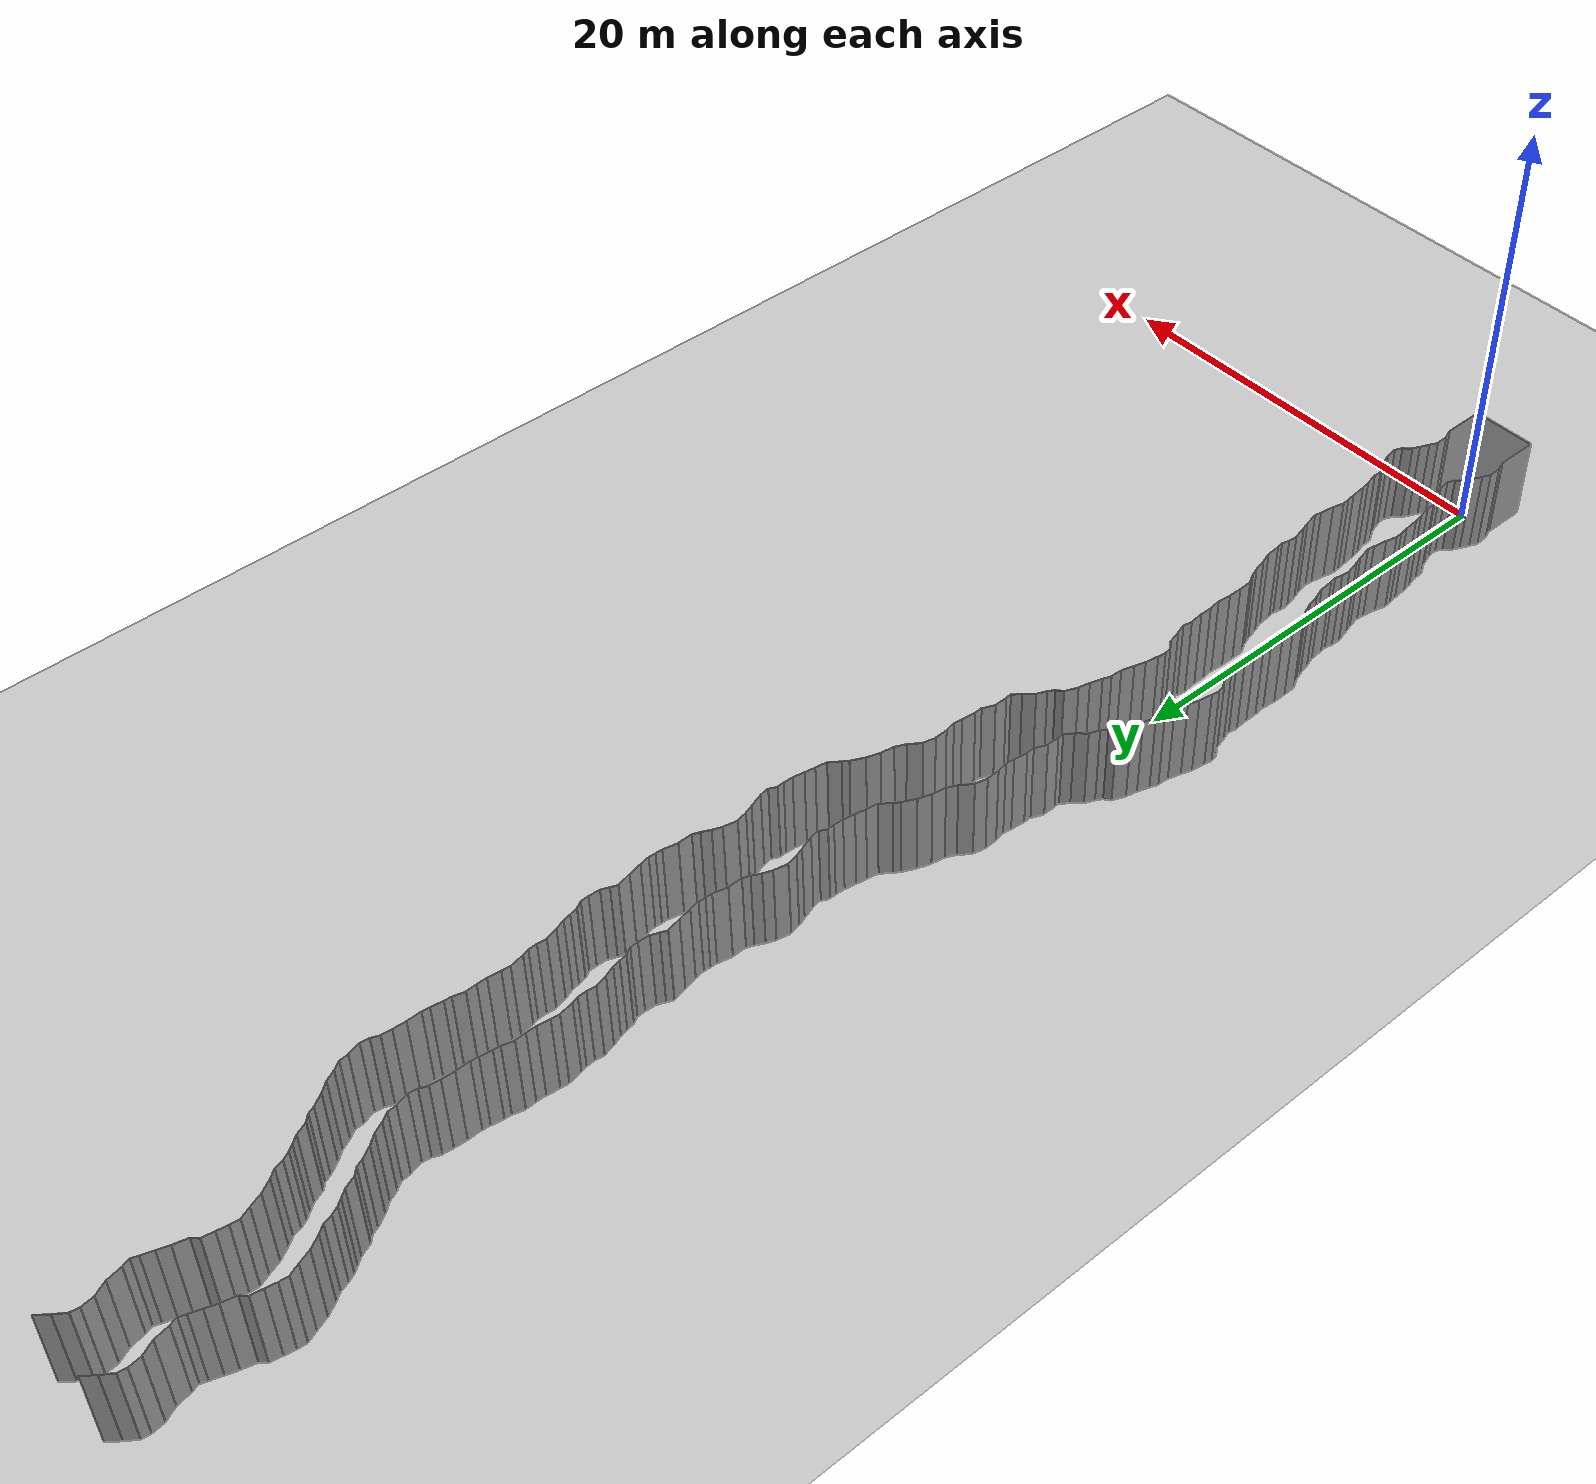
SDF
<sdf version="1.6">
 <world name="default">
  <light name="sun" type="directional">
   <pose>0 0 10 0 -0 0</pose>
   <diffuse>0.8 0.8 0.8 1</diffuse>
   <specular>0.2 0.2 0.2 1</specular>
   <attenuation>
    <range>1000</range>
    <constant>0.9</constant>
    <linear>0.01</linear>
    <quadratic>0.001</quadratic>
   </attenuation>
   <direction>-0.5 0.1 -0.9</direction>
  </light>
  <model name="ground_plane">
   <static>1</static>
   <link name="link">
    <collision name="collision">
     <geometry><plane><normal>0 0 1</normal><size>200 200</size></plane></geometry>
     <surface><friction><ode><mu>100</mu><mu2>50</mu2></ode></friction></surface>
    </collision>
    <visual name="visual">
     <cast_shadows>0</cast_shadows>
     <geometry><plane><normal>0 0 1</normal><size>200 200</size></plane></geometry>
     <material>
      <script><uri>file://media/materials/scripts/gazebo.material</uri><name>Gazebo/Grey</name></script>
     </material>
    </visual>
   </link>
   <pose>0 100 0 0 -0 0</pose>
  </model>
  <gravity>0 0 -9.8</gravity>
  <magnetic_field>6e-06 2.3e-05 -4.2e-05</magnetic_field>
  <atmosphere type="adiabatic"/>
  <physics default="0" name="default_physics" type="ode">
   <max_step_size>0.001</max_step_size>
   <real_time_factor>1</real_time_factor>
   <real_time_update_rate>1000</real_time_update_rate>
  </physics>
  <scene><ambient>0.4 0.4 0.4 1</ambient><background>0.7 0.7 0.7 1</background><shadows>1</shadows></scene>
  <spherical_coordinates>
   <surface_model>EARTH_WGS84</surface_model>
   <latitude_deg>0</latitude_deg>
   <longitude_deg>0</longitude_deg>
   <elevation>0</elevation>
   <heading_deg>0</heading_deg>
  </spherical_coordinates>
  <model name="wall_back">
   <static>1</static>
   <pose>0.0 -2 2 0.0 0 0.0</pose>
   <link name="link">
    <collision name="collision"><geometry><box><size>3 0.02 4</size></box></geometry></collision>
    <visual name="visual">
     <material>
      <script><name>Gazebo/Grey</name><uri>file://media/materials/scripts/gazebo.material</uri></script>
     </material>
     <geometry><box><size>3 0.02 4</size></box></geometry>
    </visual>
   </link>
  </model>
  <model name="wall_left">
   <static>1</static>
   <pose>1.5 -1 2 0 0 0.00</pose>
   <link name="link">
    <collision name="collision"><geometry><box><size>0.02 2 4</size></box></geometry></collision>
    <visual name="visual">
     <material>
      <script><name>Gazebo/Grey</name><uri>file://media/materials/scripts/gazebo.material</uri></script>
     </material>
     <geometry><box><size>0.02 2 4</size></box></geometry>
    </visual>
   </link>
  </model>
  <model name="wall_right">
   <static>1</static>
   <pose>-1.5 -1 2 0 0 0.00</pose>
   <link name="link">
    <collision name="collision"><geometry><box><size>0.02 2 4</size></box></geometry></collision>
    <visual name="visual">
     <material>
      <script><name>Gazebo/Grey</name><uri>file://media/materials/scripts/gazebo.material</uri></script>
     </material>
     <geometry><box><size>0.02 2 4</size></box></geometry>
    </visual>
   </link>
  </model>
  <model name="wall_0">
   <static>1</static>
   <pose>-1.5876242087305774 0.23122922117364325 2 0 0 0.3622287831516997</pose>
   <link name="link">
    <collision name="collision"><geometry><box><size>0.02 0.494550117502 4</size></box></geometry></collision>
    <visual name="visual">
     <material>
      <script><name>Gazebo/Grey</name><uri>file://media/materials/scripts/gazebo.material</uri></script>
     </material>
     <geometry><box><size>0.02 0.494550117502 4</size></box></geometry>
    </visual>
   </link>
  </model>
  <model name="wall_1">
   <static>1</static>
   <pose>1.4123757912694226 0.23122922117364325 2 0 0 0.3622287831516997</pose>
   <link name="link">
    <collision name="collision"><geometry><box><size>0.02 0.494550117502 4</size></box></geometry></collision>
    <visual name="visual">
     <material>
      <script><name>Gazebo/Grey</name><uri>file://media/materials/scripts/gazebo.material</uri></script>
     </material>
     <geometry><box><size>0.02 0.494550117502 4</size></box></geometry>
    </visual>
   </link>
  </model>
  <model name="wall_2">
   <static>1</static>
   <pose>-1.681142146697931 0.7510026568677637 2 0 0 0.020422900556318437</pose>
   <link name="link">
    <collision name="collision"><geometry><box><size>0.02 0.577208800271 4</size></box></geometry></collision>
    <visual name="visual">
     <material>
      <script><name>Gazebo/Grey</name><uri>file://media/materials/scripts/gazebo.material</uri></script>
     </material>
     <geometry><box><size>0.02 0.577208800271 4</size></box></geometry>
    </visual>
   </link>
  </model>
  <model name="wall_3">
   <static>1</static>
   <pose>1.318857853302069 0.7510026568677637 2 0 0 0.020422900556318437</pose>
   <link name="link">
    <collision name="collision"><geometry><box><size>0.02 0.577208800271 4</size></box></geometry></collision>
    <visual name="visual">
     <material>
      <script><name>Gazebo/Grey</name><uri>file://media/materials/scripts/gazebo.material</uri></script>
     </material>
     <geometry><box><size>0.02 0.577208800271 4</size></box></geometry>
    </visual>
   </link>
  </model>
  <model name="wall_4">
   <static>1</static>
   <pose>-1.6010782179631144 1.2240133101605413 2 0 0 -0.4360630841983263</pose>
   <link name="link">
    <collision name="collision"><geometry><box><size>0.02 0.407021306554 4</size></box></geometry></collision>
    <visual name="visual">
     <material>
      <script><name>Gazebo/Grey</name><uri>file://media/materials/scripts/gazebo.material</uri></script>
     </material>
     <geometry><box><size>0.02 0.407021306554 4</size></box></geometry>
    </visual>
   </link>
  </model>
  <model name="wall_5">
   <static>1</static>
   <pose>1.3989217820368856 1.2240133101605413 2 0 0 -0.4360630841983263</pose>
   <link name="link">
    <collision name="collision"><geometry><box><size>0.02 0.407021306554 4</size></box></geometry></collision>
    <visual name="visual">
     <material>
      <script><name>Gazebo/Grey</name><uri>file://media/materials/scripts/gazebo.material</uri></script>
     </material>
     <geometry><box><size>0.02 0.407021306554 4</size></box></geometry>
    </visual>
   </link>
  </model>
  <model name="wall_6">
   <static>1</static>
   <pose>-1.4237968651613715 1.6241239041570183 2 0 0 -0.40059313762966453</pose>
   <link name="link">
    <collision name="collision"><geometry><box><size>0.02 0.468369166021 4</size></box></geometry></collision>
    <visual name="visual">
     <material>
      <script><name>Gazebo/Grey</name><uri>file://media/materials/scripts/gazebo.material</uri></script>
     </material>
     <geometry><box><size>0.02 0.468369166021 4</size></box></geometry>
    </visual>
   </link>
  </model>
  <model name="wall_7">
   <static>1</static>
   <pose>1.5762031348386285 1.6241239041570183 2 0 0 -0.40059313762966453</pose>
   <link name="link">
    <collision name="collision"><geometry><box><size>0.02 0.468369166021 4</size></box></geometry></collision>
    <visual name="visual">
     <material>
      <script><name>Gazebo/Grey</name><uri>file://media/materials/scripts/gazebo.material</uri></script>
     </material>
     <geometry><box><size>0.02 0.468369166021 4</size></box></geometry>
    </visual>
   </link>
  </model>
  <model name="wall_8">
   <static>1</static>
   <pose>-1.255907765241811 1.9977645921500706 2 0 0 -0.45125334471226686</pose>
   <link name="link">
    <collision name="collision"><geometry><box><size>0.02 0.351141940665 4</size></box></geometry></collision>
    <visual name="visual">
     <material>
      <script><name>Gazebo/Grey</name><uri>file://media/materials/scripts/gazebo.material</uri></script>
     </material>
     <geometry><box><size>0.02 0.351141940665 4</size></box></geometry>
    </visual>
   </link>
  </model>
  <model name="wall_9">
   <static>1</static>
   <pose>1.744092234758189 1.9977645921500706 2 0 0 -0.45125334471226686</pose>
   <link name="link">
    <collision name="collision"><geometry><box><size>0.02 0.351141940665 4</size></box></geometry></collision>
    <visual name="visual">
     <material>
      <script><name>Gazebo/Grey</name><uri>file://media/materials/scripts/gazebo.material</uri></script>
     </material>
     <geometry><box><size>0.02 0.351141940665 4</size></box></geometry>
    </visual>
   </link>
  </model>
  <model name="wall_10">
   <static>1</static>
   <pose>-1.02719313348299 2.321697933582735 2 0 0 -0.7420798301374374</pose>
   <link name="link">
    <collision name="collision"><geometry><box><size>0.02 0.450263974333 4</size></box></geometry></collision>
    <visual name="visual">
     <material>
      <script><name>Gazebo/Grey</name><uri>file://media/materials/scripts/gazebo.material</uri></script>
     </material>
     <geometry><box><size>0.02 0.450263974333 4</size></box></geometry>
    </visual>
   </link>
  </model>
  <model name="wall_11">
   <static>1</static>
   <pose>1.97280686651701 2.321697933582735 2 0 0 -0.7420798301374374</pose>
   <link name="link">
    <collision name="collision"><geometry><box><size>0.02 0.450263974333 4</size></box></geometry></collision>
    <visual name="visual">
     <material>
      <script><name>Gazebo/Grey</name><uri>file://media/materials/scripts/gazebo.material</uri></script>
     </material>
     <geometry><box><size>0.02 0.450263974333 4</size></box></geometry>
    </visual>
   </link>
  </model>
  <model name="wall_12">
   <static>1</static>
   <pose>-0.8063411990763812 2.6633253259963277 2 0 0 -0.3727617229133646</pose>
   <link name="link">
    <collision name="collision"><geometry><box><size>0.02 0.377291628684 4</size></box></geometry></collision>
    <visual name="visual">
     <material>
      <script><name>Gazebo/Grey</name><uri>file://media/materials/scripts/gazebo.material</uri></script>
     </material>
     <geometry><box><size>0.02 0.377291628684 4</size></box></geometry>
    </visual>
   </link>
  </model>
  <model name="wall_13">
   <static>1</static>
   <pose>2.1936588009236186 2.6633253259963277 2 0 0 -0.3727617229133646</pose>
   <link name="link">
    <collision name="collision"><geometry><box><size>0.02 0.377291628684 4</size></box></geometry></collision>
    <visual name="visual">
     <material>
      <script><name>Gazebo/Grey</name><uri>file://media/materials/scripts/gazebo.material</uri></script>
     </material>
     <geometry><box><size>0.02 0.377291628684 4</size></box></geometry>
    </visual>
   </link>
  </model>
  <model name="wall_14">
   <static>1</static>
   <pose>-0.7813794864882018 3.118658401591183 2 0 0 0.15516030058365127</pose>
   <link name="link">
    <collision name="collision"><geometry><box><size>0.02 0.566085498496 4</size></box></geometry></collision>
    <visual name="visual">
     <material>
      <script><name>Gazebo/Grey</name><uri>file://media/materials/scripts/gazebo.material</uri></script>
     </material>
     <geometry><box><size>0.02 0.566085498496 4</size></box></geometry>
    </visual>
   </link>
  </model>
  <model name="wall_15">
   <static>1</static>
   <pose>2.218620513511798 3.118658401591183 2 0 0 0.15516030058365127</pose>
   <link name="link">
    <collision name="collision"><geometry><box><size>0.02 0.566085498496 4</size></box></geometry></collision>
    <visual name="visual">
     <material>
      <script><name>Gazebo/Grey</name><uri>file://media/materials/scripts/gazebo.material</uri></script>
     </material>
     <geometry><box><size>0.02 0.566085498496 4</size></box></geometry>
    </visual>
   </link>
  </model>
  <model name="wall_16">
   <static>1</static>
   <pose>-0.9129578250842095 3.6653485683726394 2 0 0 0.3177733845068075</pose>
   <link name="link">
    <collision name="collision"><geometry><box><size>0.02 0.562244998529 4</size></box></geometry></collision>
    <visual name="visual">
     <material>
      <script><name>Gazebo/Grey</name><uri>file://media/materials/scripts/gazebo.material</uri></script>
     </material>
     <geometry><box><size>0.02 0.562244998529 4</size></box></geometry>
    </visual>
   </link>
  </model>
  <model name="wall_17">
   <static>1</static>
   <pose>2.0870421749157906 3.6653485683726394 2 0 0 0.3177733845068075</pose>
   <link name="link">
    <collision name="collision"><geometry><box><size>0.02 0.562244998529 4</size></box></geometry></collision>
    <visual name="visual">
     <material>
      <script><name>Gazebo/Grey</name><uri>file://media/materials/scripts/gazebo.material</uri></script>
     </material>
     <geometry><box><size>0.02 0.562244998529 4</size></box></geometry>
    </visual>
   </link>
  </model>
  <model name="wall_18">
   <static>1</static>
   <pose>-1.16911645493446 4.216795009771947 2 0 0 0.5344049792094162</pose>
   <link name="link">
    <collision name="collision"><geometry><box><size>0.02 0.660952990226 4</size></box></geometry></collision>
    <visual name="visual">
     <material>
      <script><name>Gazebo/Grey</name><uri>file://media/materials/scripts/gazebo.material</uri></script>
     </material>
     <geometry><box><size>0.02 0.660952990226 4</size></box></geometry>
    </visual>
   </link>
  </model>
  <model name="wall_19">
   <static>1</static>
   <pose>1.83088354506554 4.216795009771947 2 0 0 0.5344049792094162</pose>
   <link name="link">
    <collision name="collision"><geometry><box><size>0.02 0.660952990226 4</size></box></geometry></collision>
    <visual name="visual">
     <material>
      <script><name>Gazebo/Grey</name><uri>file://media/materials/scripts/gazebo.material</uri></script>
     </material>
     <geometry><box><size>0.02 0.660952990226 4</size></box></geometry>
    </visual>
   </link>
  </model>
  <model name="wall_20">
   <static>1</static>
   <pose>-1.331105441448903 4.685605805069305 2 0 0 -0.03432429499593664</pose>
   <link name="link">
    <collision name="collision"><geometry><box><size>0.02 0.36904143074 4</size></box></geometry></collision>
    <visual name="visual">
     <material>
      <script><name>Gazebo/Grey</name><uri>file://media/materials/scripts/gazebo.material</uri></script>
     </material>
     <geometry><box><size>0.02 0.36904143074 4</size></box></geometry>
    </visual>
   </link>
  </model>
  <model name="wall_21">
   <static>1</static>
   <pose>1.668894558551097 4.685605805069305 2 0 0 -0.03432429499593664</pose>
   <link name="link">
    <collision name="collision"><geometry><box><size>0.02 0.36904143074 4</size></box></geometry></collision>
    <visual name="visual">
     <material>
      <script><name>Gazebo/Grey</name><uri>file://media/materials/scripts/gazebo.material</uri></script>
     </material>
     <geometry><box><size>0.02 0.36904143074 4</size></box></geometry>
    </visual>
   </link>
  </model>
  <model name="wall_22">
   <static>1</static>
   <pose>-1.4038712028018625 5.185495743198005 2 0 0 0.24566048931518805</pose>
   <link name="link">
    <collision name="collision"><geometry><box><size>0.02 0.650485401973 4</size></box></geometry></collision>
    <visual name="visual">
     <material>
      <script><name>Gazebo/Grey</name><uri>file://media/materials/scripts/gazebo.material</uri></script>
     </material>
     <geometry><box><size>0.02 0.650485401973 4</size></box></geometry>
    </visual>
   </link>
  </model>
  <model name="wall_23">
   <static>1</static>
   <pose>1.5961287971981375 5.185495743198005 2 0 0 0.24566048931518805</pose>
   <link name="link">
    <collision name="collision"><geometry><box><size>0.02 0.650485401973 4</size></box></geometry></collision>
    <visual name="visual">
     <material>
      <script><name>Gazebo/Grey</name><uri>file://media/materials/scripts/gazebo.material</uri></script>
     </material>
     <geometry><box><size>0.02 0.650485401973 4</size></box></geometry>
    </visual>
   </link>
  </model>
  <model name="wall_24">
   <static>1</static>
   <pose>-1.5147877099640366 5.708636104299 2 0 0 0.15203950040561762</pose>
   <link name="link">
    <collision name="collision"><geometry><box><size>0.02 0.420171904778 4</size></box></geometry></collision>
    <visual name="visual">
     <material>
      <script><name>Gazebo/Grey</name><uri>file://media/materials/scripts/gazebo.material</uri></script>
     </material>
     <geometry><box><size>0.02 0.420171904778 4</size></box></geometry>
    </visual>
   </link>
  </model>
  <model name="wall_25">
   <static>1</static>
   <pose>1.4852122900359634 5.708636104299 2 0 0 0.15203950040561762</pose>
   <link name="link">
    <collision name="collision"><geometry><box><size>0.02 0.420171904778 4</size></box></geometry></collision>
    <visual name="visual">
     <material>
      <script><name>Gazebo/Grey</name><uri>file://media/materials/scripts/gazebo.material</uri></script>
     </material>
     <geometry><box><size>0.02 0.420171904778 4</size></box></geometry>
    </visual>
   </link>
  </model>
  <model name="wall_26">
   <static>1</static>
   <pose>-1.5774709605451498 6.2586213639950525 2 0 0 0.08991972691887315</pose>
   <link name="link">
    <collision name="collision"><geometry><box><size>0.02 0.687422842123 4</size></box></geometry></collision>
    <visual name="visual">
     <material>
      <script><name>Gazebo/Grey</name><uri>file://media/materials/scripts/gazebo.material</uri></script>
     </material>
     <geometry><box><size>0.02 0.687422842123 4</size></box></geometry>
    </visual>
   </link>
  </model>
  <model name="wall_27">
   <static>1</static>
   <pose>1.4225290394548502 6.2586213639950525 2 0 0 0.08991972691887315</pose>
   <link name="link">
    <collision name="collision"><geometry><box><size>0.02 0.687422842123 4</size></box></geometry></collision>
    <visual name="visual">
     <material>
      <script><name>Gazebo/Grey</name><uri>file://media/materials/scripts/gazebo.material</uri></script>
     </material>
     <geometry><box><size>0.02 0.687422842123 4</size></box></geometry>
    </visual>
   </link>
  </model>
  <model name="wall_28">
   <static>1</static>
   <pose>-1.6373584938601033 6.80442644468633 2 0 0 0.14167469839129435</pose>
   <link name="link">
    <collision name="collision"><geometry><box><size>0.02 0.411083223317 4</size></box></geometry></collision>
    <visual name="visual">
     <material>
      <script><name>Gazebo/Grey</name><uri>file://media/materials/scripts/gazebo.material</uri></script>
     </material>
     <geometry><box><size>0.02 0.411083223317 4</size></box></geometry>
    </visual>
   </link>
  </model>
  <model name="wall_29">
   <static>1</static>
   <pose>1.3626415061398967 6.80442644468633 2 0 0 0.14167469839129435</pose>
   <link name="link">
    <collision name="collision"><geometry><box><size>0.02 0.411083223317 4</size></box></geometry></collision>
    <visual name="visual">
     <material>
      <script><name>Gazebo/Grey</name><uri>file://media/materials/scripts/gazebo.material</uri></script>
     </material>
     <geometry><box><size>0.02 0.411083223317 4</size></box></geometry>
    </visual>
   </link>
  </model>
  <model name="wall_30">
   <static>1</static>
   <pose>-1.6694018304596874 7.158968021976017 2 0 0 0.01999350823538828</pose>
   <link name="link">
    <collision name="collision"><geometry><box><size>0.02 0.302179003537 4</size></box></geometry></collision>
    <visual name="visual">
     <material>
      <script><name>Gazebo/Grey</name><uri>file://media/materials/scripts/gazebo.material</uri></script>
     </material>
     <geometry><box><size>0.02 0.302179003537 4</size></box></geometry>
    </visual>
   </link>
  </model>
  <model name="wall_31">
   <static>1</static>
   <pose>1.3305981695403126 7.158968021976017 2 0 0 0.01999350823538828</pose>
   <link name="link">
    <collision name="collision"><geometry><box><size>0.02 0.302179003537 4</size></box></geometry></collision>
    <visual name="visual">
     <material>
      <script><name>Gazebo/Grey</name><uri>file://media/materials/scripts/gazebo.material</uri></script>
     </material>
     <geometry><box><size>0.02 0.302179003537 4</size></box></geometry>
    </visual>
   </link>
  </model>
  <model name="wall_32">
   <static>1</static>
   <pose>-1.60668591949283 7.577563180676779 2 0 0 -0.24093796002070506</pose>
   <link name="link">
    <collision name="collision"><geometry><box><size>0.02 0.550987198429 4</size></box></geometry></collision>
    <visual name="visual">
     <material>
      <script><name>Gazebo/Grey</name><uri>file://media/materials/scripts/gazebo.material</uri></script>
     </material>
     <geometry><box><size>0.02 0.550987198429 4</size></box></geometry>
    </visual>
   </link>
  </model>
  <model name="wall_33">
   <static>1</static>
   <pose>1.39331408050717 7.577563180676779 2 0 0 -0.24093796002070506</pose>
   <link name="link">
    <collision name="collision"><geometry><box><size>0.02 0.550987198429 4</size></box></geometry></collision>
    <visual name="visual">
     <material>
      <script><name>Gazebo/Grey</name><uri>file://media/materials/scripts/gazebo.material</uri></script>
     </material>
     <geometry><box><size>0.02 0.550987198429 4</size></box></geometry>
    </visual>
   </link>
  </model>
  <model name="wall_34">
   <static>1</static>
   <pose>-1.487517134799927 8.177891859906683 2 0 0 -0.15919845278859174</pose>
   <link name="link">
    <collision name="collision"><geometry><box><size>0.02 0.674109995206 4</size></box></geometry></collision>
    <visual name="visual">
     <material>
      <script><name>Gazebo/Grey</name><uri>file://media/materials/scripts/gazebo.material</uri></script>
     </material>
     <geometry><box><size>0.02 0.674109995206 4</size></box></geometry>
    </visual>
   </link>
  </model>
  <model name="wall_35">
   <static>1</static>
   <pose>1.512482865200073 8.177891859906683 2 0 0 -0.15919845278859174</pose>
   <link name="link">
    <collision name="collision"><geometry><box><size>0.02 0.674109995206 4</size></box></geometry></collision>
    <visual name="visual">
     <material>
      <script><name>Gazebo/Grey</name><uri>file://media/materials/scripts/gazebo.material</uri></script>
     </material>
     <geometry><box><size>0.02 0.674109995206 4</size></box></geometry>
    </visual>
   </link>
  </model>
  <model name="wall_36">
   <static>1</static>
   <pose>-1.412522938305828 8.683055036649566 2 0 0 -0.12444431391176167</pose>
   <link name="link">
    <collision name="collision"><geometry><box><size>0.02 0.347427431331 4</size></box></geometry></collision>
    <visual name="visual">
     <material>
      <script><name>Gazebo/Grey</name><uri>file://media/materials/scripts/gazebo.material</uri></script>
     </material>
     <geometry><box><size>0.02 0.347427431331 4</size></box></geometry>
    </visual>
   </link>
  </model>
  <model name="wall_37">
   <static>1</static>
   <pose>1.587477061694172 8.683055036649566 2 0 0 -0.12444431391176167</pose>
   <link name="link">
    <collision name="collision"><geometry><box><size>0.02 0.347427431331 4</size></box></geometry></collision>
    <visual name="visual">
     <material>
      <script><name>Gazebo/Grey</name><uri>file://media/materials/scripts/gazebo.material</uri></script>
     </material>
     <geometry><box><size>0.02 0.347427431331 4</size></box></geometry>
    </visual>
   </link>
  </model>
  <model name="wall_38">
   <static>1</static>
   <pose>-1.4709376676508863 9.189374222242328 2 0 0 0.23506058787245998</pose>
   <link name="link">
    <collision name="collision"><geometry><box><size>0.02 0.686784070273 4</size></box></geometry></collision>
    <visual name="visual">
     <material>
      <script><name>Gazebo/Grey</name><uri>file://media/materials/scripts/gazebo.material</uri></script>
     </material>
     <geometry><box><size>0.02 0.686784070273 4</size></box></geometry>
    </visual>
   </link>
  </model>
  <model name="wall_39">
   <static>1</static>
   <pose>1.5290623323491137 9.189374222242328 2 0 0 0.23506058787245998</pose>
   <link name="link">
    <collision name="collision"><geometry><box><size>0.02 0.686784070273 4</size></box></geometry></collision>
    <visual name="visual">
     <material>
      <script><name>Gazebo/Grey</name><uri>file://media/materials/scripts/gazebo.material</uri></script>
     </material>
     <geometry><box><size>0.02 0.686784070273 4</size></box></geometry>
    </visual>
   </link>
  </model>
  <model name="wall_40">
   <static>1</static>
   <pose>-1.6040678549878593 9.703110389431103 2 0 0 0.2874581484592028</pose>
   <link name="link">
    <collision name="collision"><geometry><box><size>0.02 0.374960172206 4</size></box></geometry></collision>
    <visual name="visual">
     <material>
      <script><name>Gazebo/Grey</name><uri>file://media/materials/scripts/gazebo.material</uri></script>
     </material>
     <geometry><box><size>0.02 0.374960172206 4</size></box></geometry>
    </visual>
   </link>
  </model>
  <model name="wall_41">
   <static>1</static>
   <pose>1.3959321450121407 9.703110389431103 2 0 0 0.2874581484592028</pose>
   <link name="link">
    <collision name="collision"><geometry><box><size>0.02 0.374960172206 4</size></box></geometry></collision>
    <visual name="visual">
     <material>
      <script><name>Gazebo/Grey</name><uri>file://media/materials/scripts/gazebo.material</uri></script>
     </material>
     <geometry><box><size>0.02 0.374960172206 4</size></box></geometry>
    </visual>
   </link>
  </model>
  <model name="wall_42">
   <static>1</static>
   <pose>-1.7329389687149759 10.197243570213887 2 0 0 0.23637074936883762</pose>
   <link name="link">
    <collision name="collision"><geometry><box><size>0.02 0.646672914891 4</size></box></geometry></collision>
    <visual name="visual">
     <material>
      <script><name>Gazebo/Grey</name><uri>file://media/materials/scripts/gazebo.material</uri></script>
     </material>
     <geometry><box><size>0.02 0.646672914891 4</size></box></geometry>
    </visual>
   </link>
  </model>
  <model name="wall_43">
   <static>1</static>
   <pose>1.2670610312850241 10.197243570213887 2 0 0 0.23637074936883762</pose>
   <link name="link">
    <collision name="collision"><geometry><box><size>0.02 0.646672914891 4</size></box></geometry></collision>
    <visual name="visual">
     <material>
      <script><name>Gazebo/Grey</name><uri>file://media/materials/scripts/gazebo.material</uri></script>
     </material>
     <geometry><box><size>0.02 0.646672914891 4</size></box></geometry>
    </visual>
   </link>
  </model>
  <model name="wall_44">
   <static>1</static>
   <pose>-1.7885054831007305 10.713606101822911 2 0 0 -0.09942066980862506</pose>
   <link name="link">
    <collision name="collision"><geometry><box><size>0.02 0.406038453251 4</size></box></geometry></collision>
    <visual name="visual">
     <material>
      <script><name>Gazebo/Grey</name><uri>file://media/materials/scripts/gazebo.material</uri></script>
     </material>
     <geometry><box><size>0.02 0.406038453251 4</size></box></geometry>
    </visual>
   </link>
  </model>
  <model name="wall_45">
   <static>1</static>
   <pose>1.2114945168992695 10.713606101822911 2 0 0 -0.09942066980862506</pose>
   <link name="link">
    <collision name="collision"><geometry><box><size>0.02 0.406038453251 4</size></box></geometry></collision>
    <visual name="visual">
     <material>
      <script><name>Gazebo/Grey</name><uri>file://media/materials/scripts/gazebo.material</uri></script>
     </material>
     <geometry><box><size>0.02 0.406038453251 4</size></box></geometry>
    </visual>
   </link>
  </model>
  <model name="wall_46">
   <static>1</static>
   <pose>-1.7268397135744855 11.09805291973203 2 0 0 -0.22375441806541252</pose>
   <link name="link">
    <collision name="collision"><geometry><box><size>0.02 0.374188315208 4</size></box></geometry></collision>
    <visual name="visual">
     <material>
      <script><name>Gazebo/Grey</name><uri>file://media/materials/scripts/gazebo.material</uri></script>
     </material>
     <geometry><box><size>0.02 0.374188315208 4</size></box></geometry>
    </visual>
   </link>
  </model>
  <model name="wall_47">
   <static>1</static>
   <pose>1.2731602864255145 11.09805291973203 2 0 0 -0.22375441806541252</pose>
   <link name="link">
    <collision name="collision"><geometry><box><size>0.02 0.374188315208 4</size></box></geometry></collision>
    <visual name="visual">
     <material>
      <script><name>Gazebo/Grey</name><uri>file://media/materials/scripts/gazebo.material</uri></script>
     </material>
     <geometry><box><size>0.02 0.374188315208 4</size></box></geometry>
    </visual>
   </link>
  </model>
  <model name="wall_48">
   <static>1</static>
   <pose>-1.712931874517814 11.438604195088564 2 0 0 0.1728508186799411</pose>
   <link name="link">
    <collision name="collision"><geometry><box><size>0.02 0.321026067793 4</size></box></geometry></collision>
    <visual name="visual">
     <material>
      <script><name>Gazebo/Grey</name><uri>file://media/materials/scripts/gazebo.material</uri></script>
     </material>
     <geometry><box><size>0.02 0.321026067793 4</size></box></geometry>
    </visual>
   </link>
  </model>
  <model name="wall_49">
   <static>1</static>
   <pose>1.287068125482186 11.438604195088564 2 0 0 0.1728508186799411</pose>
   <link name="link">
    <collision name="collision"><geometry><box><size>0.02 0.321026067793 4</size></box></geometry></collision>
    <visual name="visual">
     <material>
      <script><name>Gazebo/Grey</name><uri>file://media/materials/scripts/gazebo.material</uri></script>
     </material>
     <geometry><box><size>0.02 0.321026067793 4</size></box></geometry>
    </visual>
   </link>
  </model>
  <model name="wall_50">
   <static>1</static>
   <pose>-1.7701084362684687 11.92697386785074 2 0 0 0.08929959817835817</pose>
   <link name="link">
    <collision name="collision"><geometry><box><size>0.02 0.663139381106 4</size></box></geometry></collision>
    <visual name="visual">
     <material>
      <script><name>Gazebo/Grey</name><uri>file://media/materials/scripts/gazebo.material</uri></script>
     </material>
     <geometry><box><size>0.02 0.663139381106 4</size></box></geometry>
    </visual>
   </link>
  </model>
  <model name="wall_51">
   <static>1</static>
   <pose>1.2298915637315313 11.92697386785074 2 0 0 0.08929959817835817</pose>
   <link name="link">
    <collision name="collision"><geometry><box><size>0.02 0.663139381106 4</size></box></geometry></collision>
    <visual name="visual">
     <material>
      <script><name>Gazebo/Grey</name><uri>file://media/materials/scripts/gazebo.material</uri></script>
     </material>
     <geometry><box><size>0.02 0.663139381106 4</size></box></geometry>
    </visual>
   </link>
  </model>
  <model name="wall_52">
   <static>1</static>
   <pose>-1.8816833254051153 12.50215341112657 2 0 0 0.32307835433799564</pose>
   <link name="link">
    <collision name="collision"><geometry><box><size>0.02 0.516589009522 4</size></box></geometry></collision>
    <visual name="visual">
     <material>
      <script><name>Gazebo/Grey</name><uri>file://media/materials/scripts/gazebo.material</uri></script>
     </material>
     <geometry><box><size>0.02 0.516589009522 4</size></box></geometry>
    </visual>
   </link>
  </model>
  <model name="wall_53">
   <static>1</static>
   <pose>1.1183166745948847 12.50215341112657 2 0 0 0.32307835433799564</pose>
   <link name="link">
    <collision name="collision"><geometry><box><size>0.02 0.516589009522 4</size></box></geometry></collision>
    <visual name="visual">
     <material>
      <script><name>Gazebo/Grey</name><uri>file://media/materials/scripts/gazebo.material</uri></script>
     </material>
     <geometry><box><size>0.02 0.516589009522 4</size></box></geometry>
    </visual>
   </link>
  </model>
  <model name="wall_54">
   <static>1</static>
   <pose>-2.0352472689060357 13.041144281243845 2 0 0 0.23870783770549567</pose>
   <link name="link">
    <collision name="collision"><geometry><box><size>0.02 0.605282928543 4</size></box></geometry></collision>
    <visual name="visual">
     <material>
      <script><name>Gazebo/Grey</name><uri>file://media/materials/scripts/gazebo.material</uri></script>
     </material>
     <geometry><box><size>0.02 0.605282928543 4</size></box></geometry>
    </visual>
   </link>
  </model>
  <model name="wall_55">
   <static>1</static>
   <pose>0.9647527310939643 13.041144281243845 2 0 0 0.23870783770549567</pose>
   <link name="link">
    <collision name="collision"><geometry><box><size>0.02 0.605282928543 4</size></box></geometry></collision>
    <visual name="visual">
     <material>
      <script><name>Gazebo/Grey</name><uri>file://media/materials/scripts/gazebo.material</uri></script>
     </material>
     <geometry><box><size>0.02 0.605282928543 4</size></box></geometry>
    </visual>
   </link>
  </model>
  <model name="wall_56">
   <static>1</static>
   <pose>-2.181981559114251 13.533577426280555 2 0 0 0.36223788628466375</pose>
   <link name="link">
    <collision name="collision"><geometry><box><size>0.02 0.424279727035 4</size></box></geometry></collision>
    <visual name="visual">
     <material>
      <script><name>Gazebo/Grey</name><uri>file://media/materials/scripts/gazebo.material</uri></script>
     </material>
     <geometry><box><size>0.02 0.424279727035 4</size></box></geometry>
    </visual>
   </link>
  </model>
  <model name="wall_57">
   <static>1</static>
   <pose>0.8180184408857492 13.533577426280555 2 0 0 0.36223788628466375</pose>
   <link name="link">
    <collision name="collision"><geometry><box><size>0.02 0.424279727035 4</size></box></geometry></collision>
    <visual name="visual">
     <material>
      <script><name>Gazebo/Grey</name><uri>file://media/materials/scripts/gazebo.material</uri></script>
     </material>
     <geometry><box><size>0.02 0.424279727035 4</size></box></geometry>
    </visual>
   </link>
  </model>
  <model name="wall_58">
   <static>1</static>
   <pose>-2.3720656886717433 13.938891062008437 2 0 0 0.5068833346539584</pose>
   <link name="link">
    <collision name="collision"><geometry><box><size>0.02 0.473405929821 4</size></box></geometry></collision>
    <visual name="visual">
     <material>
      <script><name>Gazebo/Grey</name><uri>file://media/materials/scripts/gazebo.material</uri></script>
     </material>
     <geometry><box><size>0.02 0.473405929821 4</size></box></geometry>
    </visual>
   </link>
  </model>
  <model name="wall_59">
   <static>1</static>
   <pose>0.6279343113282567 13.938891062008437 2 0 0 0.5068833346539584</pose>
   <link name="link">
    <collision name="collision"><geometry><box><size>0.02 0.473405929821 4</size></box></geometry></collision>
    <visual name="visual">
     <material>
      <script><name>Gazebo/Grey</name><uri>file://media/materials/scripts/gazebo.material</uri></script>
     </material>
     <geometry><box><size>0.02 0.473405929821 4</size></box></geometry>
    </visual>
   </link>
  </model>
  <model name="wall_60">
   <static>1</static>
   <pose>-2.4952888274189093 14.45307274430188 2 0 0 0.027055320883748808</pose>
   <link name="link">
    <collision name="collision"><geometry><box><size>0.02 0.614707633505 4</size></box></geometry></collision>
    <visual name="visual">
     <material>
      <script><name>Gazebo/Grey</name><uri>file://media/materials/scripts/gazebo.material</uri></script>
     </material>
     <geometry><box><size>0.02 0.614707633505 4</size></box></geometry>
    </visual>
   </link>
  </model>
  <model name="wall_61">
   <static>1</static>
   <pose>0.5047111725810907 14.45307274430188 2 0 0 0.027055320883748808</pose>
   <link name="link">
    <collision name="collision"><geometry><box><size>0.02 0.614707633505 4</size></box></geometry></collision>
    <visual name="visual">
     <material>
      <script><name>Gazebo/Grey</name><uri>file://media/materials/scripts/gazebo.material</uri></script>
     </material>
     <geometry><box><size>0.02 0.614707633505 4</size></box></geometry>
    </visual>
   </link>
  </model>
  <model name="wall_62">
   <static>1</static>
   <pose>-2.499990943019349 15.072449960833302 2 0 0 -0.011572731674872171</pose>
   <link name="link">
    <collision name="collision"><geometry><box><size>0.02 0.624313571979 4</size></box></geometry></collision>
    <visual name="visual">
     <material>
      <script><name>Gazebo/Grey</name><uri>file://media/materials/scripts/gazebo.material</uri></script>
     </material>
     <geometry><box><size>0.02 0.624313571979 4</size></box></geometry>
    </visual>
   </link>
  </model>
  <model name="wall_63">
   <static>1</static>
   <pose>0.5000090569806508 15.072449960833302 2 0 0 -0.011572731674872171</pose>
   <link name="link">
    <collision name="collision"><geometry><box><size>0.02 0.624313571979 4</size></box></geometry></collision>
    <visual name="visual">
     <material>
      <script><name>Gazebo/Grey</name><uri>file://media/materials/scripts/gazebo.material</uri></script>
     </material>
     <geometry><box><size>0.02 0.624313571979 4</size></box></geometry>
    </visual>
   </link>
  </model>
  <model name="wall_64">
   <static>1</static>
   <pose>-2.4647111280425635 15.69189225065522 2 0 0 -0.10268580669380363</pose>
   <link name="link">
    <collision name="collision"><geometry><box><size>0.02 0.617867465502 4</size></box></geometry></collision>
    <visual name="visual">
     <material>
      <script><name>Gazebo/Grey</name><uri>file://media/materials/scripts/gazebo.material</uri></script>
     </material>
     <geometry><box><size>0.02 0.617867465502 4</size></box></geometry>
    </visual>
   </link>
  </model>
  <model name="wall_65">
   <static>1</static>
   <pose>0.5352888719574365 15.69189225065522 2 0 0 -0.10268580669380363</pose>
   <link name="link">
    <collision name="collision"><geometry><box><size>0.02 0.617867465502 4</size></box></geometry></collision>
    <visual name="visual">
     <material>
      <script><name>Gazebo/Grey</name><uri>file://media/materials/scripts/gazebo.material</uri></script>
     </material>
     <geometry><box><size>0.02 0.617867465502 4</size></box></geometry>
    </visual>
   </link>
  </model>
  <model name="wall_66">
   <static>1</static>
   <pose>-2.4679788271992855 16.277859687895326 2 0 0 0.12471700563986159</pose>
   <link name="link">
    <collision name="collision"><geometry><box><size>0.02 0.561684716599 4</size></box></geometry></collision>
    <visual name="visual">
     <material>
      <script><name>Gazebo/Grey</name><uri>file://media/materials/scripts/gazebo.material</uri></script>
     </material>
     <geometry><box><size>0.02 0.561684716599 4</size></box></geometry>
    </visual>
   </link>
  </model>
  <model name="wall_67">
   <static>1</static>
   <pose>0.5320211728007145 16.277859687895326 2 0 0 0.12471700563986159</pose>
   <link name="link">
    <collision name="collision"><geometry><box><size>0.02 0.561684716599 4</size></box></geometry></collision>
    <visual name="visual">
     <material>
      <script><name>Gazebo/Grey</name><uri>file://media/materials/scripts/gazebo.material</uri></script>
     </material>
     <geometry><box><size>0.02 0.561684716599 4</size></box></geometry>
    </visual>
   </link>
  </model>
  <model name="wall_68">
   <static>1</static>
   <pose>-2.498371072976488 16.830205705115194 2 0 0 -0.016597275477892057</pose>
   <link name="link">
    <collision name="collision"><geometry><box><size>0.02 0.547445374265 4</size></box></geometry></collision>
    <visual name="visual">
     <material>
      <script><name>Gazebo/Grey</name><uri>file://media/materials/scripts/gazebo.material</uri></script>
     </material>
     <geometry><box><size>0.02 0.547445374265 4</size></box></geometry>
    </visual>
   </link>
  </model>
  <model name="wall_69">
   <static>1</static>
   <pose>0.5016289270235119 16.830205705115194 2 0 0 -0.016597275477892057</pose>
   <link name="link">
    <collision name="collision"><geometry><box><size>0.02 0.547445374265 4</size></box></geometry></collision>
    <visual name="visual">
     <material>
      <script><name>Gazebo/Grey</name><uri>file://media/materials/scripts/gazebo.material</uri></script>
     </material>
     <geometry><box><size>0.02 0.547445374265 4</size></box></geometry>
    </visual>
   </link>
  </model>
  <model name="wall_70">
   <static>1</static>
   <pose>-2.522846252412302 17.420816195063075 2 0 0 0.09130643256531172</pose>
   <link name="link">
    <collision name="collision"><geometry><box><size>0.02 0.636502380477 4</size></box></geometry></collision>
    <visual name="visual">
     <material>
      <script><name>Gazebo/Grey</name><uri>file://media/materials/scripts/gazebo.material</uri></script>
     </material>
     <geometry><box><size>0.02 0.636502380477 4</size></box></geometry>
    </visual>
   </link>
  </model>
  <model name="wall_71">
   <static>1</static>
   <pose>0.4771537475876979 17.420816195063075 2 0 0 0.09130643256531172</pose>
   <link name="link">
    <collision name="collision"><geometry><box><size>0.02 0.636502380477 4</size></box></geometry></collision>
    <visual name="visual">
     <material>
      <script><name>Gazebo/Grey</name><uri>file://media/materials/scripts/gazebo.material</uri></script>
     </material>
     <geometry><box><size>0.02 0.636502380477 4</size></box></geometry>
    </visual>
   </link>
  </model>
  <model name="wall_72">
   <static>1</static>
   <pose>-2.5143831706178212 17.948344836911566 2 0 0 -0.1761262419085541</pose>
   <link name="link">
    <collision name="collision"><geometry><box><size>0.02 0.427824801418 4</size></box></geometry></collision>
    <visual name="visual">
     <material>
      <script><name>Gazebo/Grey</name><uri>file://media/materials/scripts/gazebo.material</uri></script>
     </material>
     <geometry><box><size>0.02 0.427824801418 4</size></box></geometry>
    </visual>
   </link>
  </model>
  <model name="wall_73">
   <static>1</static>
   <pose>0.48561682938217876 17.948344836911566 2 0 0 -0.1761262419085541</pose>
   <link name="link">
    <collision name="collision"><geometry><box><size>0.02 0.427824801418 4</size></box></geometry></collision>
    <visual name="visual">
     <material>
      <script><name>Gazebo/Grey</name><uri>file://media/materials/scripts/gazebo.material</uri></script>
     </material>
     <geometry><box><size>0.02 0.427824801418 4</size></box></geometry>
    </visual>
   </link>
  </model>
  <model name="wall_74">
   <static>1</static>
   <pose>-2.5577974521057794 18.39851629489855 2 0 0 0.32564977725428645</pose>
   <link name="link">
    <collision name="collision"><geometry><box><size>0.02 0.505715504554 4</size></box></geometry></collision>
    <visual name="visual">
     <material>
      <script><name>Gazebo/Grey</name><uri>file://media/materials/scripts/gazebo.material</uri></script>
     </material>
     <geometry><box><size>0.02 0.505715504554 4</size></box></geometry>
    </visual>
   </link>
  </model>
  <model name="wall_75">
   <static>1</static>
   <pose>0.44220254789422064 18.39851629489855 2 0 0 0.32564977725428645</pose>
   <link name="link">
    <collision name="collision"><geometry><box><size>0.02 0.505715504554 4</size></box></geometry></collision>
    <visual name="visual">
     <material>
      <script><name>Gazebo/Grey</name><uri>file://media/materials/scripts/gazebo.material</uri></script>
     </material>
     <geometry><box><size>0.02 0.505715504554 4</size></box></geometry>
    </visual>
   </link>
  </model>
  <model name="wall_76">
   <static>1</static>
   <pose>-2.7177749737235346 18.9368754607309 2 0 0 0.25874099727943234</pose>
   <link name="link">
    <collision name="collision"><geometry><box><size>0.02 0.618158408024 4</size></box></geometry></collision>
    <visual name="visual">
     <material>
      <script><name>Gazebo/Grey</name><uri>file://media/materials/scripts/gazebo.material</uri></script>
     </material>
     <geometry><box><size>0.02 0.618158408024 4</size></box></geometry>
    </visual>
   </link>
  </model>
  <model name="wall_77">
   <static>1</static>
   <pose>0.2822250262764654 18.9368754607309 2 0 0 0.25874099727943234</pose>
   <link name="link">
    <collision name="collision"><geometry><box><size>0.02 0.618158408024 4</size></box></geometry></collision>
    <visual name="visual">
     <material>
      <script><name>Gazebo/Grey</name><uri>file://media/materials/scripts/gazebo.material</uri></script>
     </material>
     <geometry><box><size>0.02 0.618158408024 4</size></box></geometry>
    </visual>
   </link>
  </model>
  <model name="wall_78">
   <static>1</static>
   <pose>-2.9493755194007756 19.410305596714846 2 0 0 0.7178855796985041</pose>
   <link name="link">
    <collision name="collision"><geometry><box><size>0.02 0.463727275413 4</size></box></geometry></collision>
    <visual name="visual">
     <material>
      <script><name>Gazebo/Grey</name><uri>file://media/materials/scripts/gazebo.material</uri></script>
     </material>
     <geometry><box><size>0.02 0.463727275413 4</size></box></geometry>
    </visual>
   </link>
  </model>
  <model name="wall_79">
   <static>1</static>
   <pose>0.05062448059922442 19.410305596714846 2 0 0 0.7178855796985041</pose>
   <link name="link">
    <collision name="collision"><geometry><box><size>0.02 0.463727275413 4</size></box></geometry></collision>
    <visual name="visual">
     <material>
      <script><name>Gazebo/Grey</name><uri>file://media/materials/scripts/gazebo.material</uri></script>
     </material>
     <geometry><box><size>0.02 0.463727275413 4</size></box></geometry>
    </visual>
   </link>
  </model>
  <model name="wall_80">
   <static>1</static>
   <pose>-3.1224642835979983 19.74097408407429 2 0 0 0.13108063142375748</pose>
   <link name="link">
    <collision name="collision"><geometry><box><size>0.02 0.314758638549 4</size></box></geometry></collision>
    <visual name="visual">
     <material>
      <script><name>Gazebo/Grey</name><uri>file://media/materials/scripts/gazebo.material</uri></script>
     </material>
     <geometry><box><size>0.02 0.314758638549 4</size></box></geometry>
    </visual>
   </link>
  </model>
  <model name="wall_81">
   <static>1</static>
   <pose>-0.12246428359799832 19.74097408407429 2 0 0 0.13108063142375748</pose>
   <link name="link">
    <collision name="collision"><geometry><box><size>0.02 0.314758638549 4</size></box></geometry></collision>
    <visual name="visual">
     <material>
      <script><name>Gazebo/Grey</name><uri>file://media/materials/scripts/gazebo.material</uri></script>
     </material>
     <geometry><box><size>0.02 0.314758638549 4</size></box></geometry>
    </visual>
   </link>
  </model>
  <model name="wall_82">
   <static>1</static>
   <pose>-3.1129655708371335 20.08389745159527 2 0 0 -0.1595211788571715</pose>
   <link name="link">
    <collision name="collision"><geometry><box><size>0.02 0.378595189887 4</size></box></geometry></collision>
    <visual name="visual">
     <material>
      <script><name>Gazebo/Grey</name><uri>file://media/materials/scripts/gazebo.material</uri></script>
     </material>
     <geometry><box><size>0.02 0.378595189887 4</size></box></geometry>
    </visual>
   </link>
  </model>
  <model name="wall_83">
   <static>1</static>
   <pose>-0.11296557083713354 20.08389745159527 2 0 0 -0.1595211788571715</pose>
   <link name="link">
    <collision name="collision"><geometry><box><size>0.02 0.378595189887 4</size></box></geometry></collision>
    <visual name="visual">
     <material>
      <script><name>Gazebo/Grey</name><uri>file://media/materials/scripts/gazebo.material</uri></script>
     </material>
     <geometry><box><size>0.02 0.378595189887 4</size></box></geometry>
    </visual>
   </link>
  </model>
  <model name="wall_84">
   <static>1</static>
   <pose>-3.030855290555757 20.57789374265384 2 0 0 -0.16786428680608062</pose>
   <link name="link">
    <collision name="collision"><geometry><box><size>0.02 0.622960675578 4</size></box></geometry></collision>
    <visual name="visual">
     <material>
      <script><name>Gazebo/Grey</name><uri>file://media/materials/scripts/gazebo.material</uri></script>
     </material>
     <geometry><box><size>0.02 0.622960675578 4</size></box></geometry>
    </visual>
   </link>
  </model>
  <model name="wall_85">
   <static>1</static>
   <pose>-0.030855290555757087 20.57789374265384 2 0 0 -0.16786428680608062</pose>
   <link name="link">
    <collision name="collision"><geometry><box><size>0.02 0.622960675578 4</size></box></geometry></collision>
    <visual name="visual">
     <material>
      <script><name>Gazebo/Grey</name><uri>file://media/materials/scripts/gazebo.material</uri></script>
     </material>
     <geometry><box><size>0.02 0.622960675578 4</size></box></geometry>
    </visual>
   </link>
  </model>
  <model name="wall_86">
   <static>1</static>
   <pose>-2.9006292514241028 21.135343340064225 2 0 0 -0.30270741947423524</pose>
   <link name="link">
    <collision name="collision"><geometry><box><size>0.02 0.524544472162 4</size></box></geometry></collision>
    <visual name="visual">
     <material>
      <script><name>Gazebo/Grey</name><uri>file://media/materials/scripts/gazebo.material</uri></script>
     </material>
     <geometry><box><size>0.02 0.524544472162 4</size></box></geometry>
    </visual>
   </link>
  </model>
  <model name="wall_87">
   <static>1</static>
   <pose>0.09937074857589723 21.135343340064225 2 0 0 -0.30270741947423524</pose>
   <link name="link">
    <collision name="collision"><geometry><box><size>0.02 0.524544472162 4</size></box></geometry></collision>
    <visual name="visual">
     <material>
      <script><name>Gazebo/Grey</name><uri>file://media/materials/scripts/gazebo.material</uri></script>
     </material>
     <geometry><box><size>0.02 0.524544472162 4</size></box></geometry>
    </visual>
   </link>
  </model>
  <model name="wall_88">
   <static>1</static>
   <pose>-2.7397760829196005 21.682706921311766 2 0 0 -0.2714589706400116</pose>
   <link name="link">
    <collision name="collision"><geometry><box><size>0.02 0.616612103579 4</size></box></geometry></collision>
    <visual name="visual">
     <material>
      <script><name>Gazebo/Grey</name><uri>file://media/materials/scripts/gazebo.material</uri></script>
     </material>
     <geometry><box><size>0.02 0.616612103579 4</size></box></geometry>
    </visual>
   </link>
  </model>
  <model name="wall_89">
   <static>1</static>
   <pose>0.2602239170803995 21.682706921311766 2 0 0 -0.2714589706400116</pose>
   <link name="link">
    <collision name="collision"><geometry><box><size>0.02 0.616612103579 4</size></box></geometry></collision>
    <visual name="visual">
     <material>
      <script><name>Gazebo/Grey</name><uri>file://media/materials/scripts/gazebo.material</uri></script>
     </material>
     <geometry><box><size>0.02 0.616612103579 4</size></box></geometry>
    </visual>
   </link>
  </model>
  <model name="wall_90">
   <static>1</static>
   <pose>-2.6460774361162382 22.24322720459198 2 0 0 -0.041835652240367435</pose>
   <link name="link">
    <collision name="collision"><geometry><box><size>0.02 0.527469883162 4</size></box></geometry></collision>
    <visual name="visual">
     <material>
      <script><name>Gazebo/Grey</name><uri>file://media/materials/scripts/gazebo.material</uri></script>
     </material>
     <geometry><box><size>0.02 0.527469883162 4</size></box></geometry>
    </visual>
   </link>
  </model>
  <model name="wall_91">
   <static>1</static>
   <pose>0.35392256388376175 22.24322720459198 2 0 0 -0.041835652240367435</pose>
   <link name="link">
    <collision name="collision"><geometry><box><size>0.02 0.527469883162 4</size></box></geometry></collision>
    <visual name="visual">
     <material>
      <script><name>Gazebo/Grey</name><uri>file://media/materials/scripts/gazebo.material</uri></script>
     </material>
     <geometry><box><size>0.02 0.527469883162 4</size></box></geometry>
    </visual>
   </link>
  </model>
  <model name="wall_92">
   <static>1</static>
   <pose>-2.5668960391070046 22.695534877558856 2 0 0 -0.3464079077855175</pose>
   <link name="link">
    <collision name="collision"><geometry><box><size>0.02 0.401454012687 4</size></box></geometry></collision>
    <visual name="visual">
     <material>
      <script><name>Gazebo/Grey</name><uri>file://media/materials/scripts/gazebo.material</uri></script>
     </material>
     <geometry><box><size>0.02 0.401454012687 4</size></box></geometry>
    </visual>
   </link>
  </model>
  <model name="wall_93">
   <static>1</static>
   <pose>0.4331039608929954 22.695534877558856 2 0 0 -0.3464079077855175</pose>
   <link name="link">
    <collision name="collision"><geometry><box><size>0.02 0.401454012687 4</size></box></geometry></collision>
    <visual name="visual">
     <material>
      <script><name>Gazebo/Grey</name><uri>file://media/materials/scripts/gazebo.material</uri></script>
     </material>
     <geometry><box><size>0.02 0.401454012687 4</size></box></geometry>
    </visual>
   </link>
  </model>
  <model name="wall_94">
   <static>1</static>
   <pose>-2.413424180653308 23.16207593375481 2 0 0 -0.2980484412434623</pose>
   <link name="link">
    <collision name="collision"><geometry><box><size>0.02 0.581094780806 4</size></box></geometry></collision>
    <visual name="visual">
     <material>
      <script><name>Gazebo/Grey</name><uri>file://media/materials/scripts/gazebo.material</uri></script>
     </material>
     <geometry><box><size>0.02 0.581094780806 4</size></box></geometry>
    </visual>
   </link>
  </model>
  <model name="wall_95">
   <static>1</static>
   <pose>0.5865758193466921 23.16207593375481 2 0 0 -0.2980484412434623</pose>
   <link name="link">
    <collision name="collision"><geometry><box><size>0.02 0.581094780806 4</size></box></geometry></collision>
    <visual name="visual">
     <material>
      <script><name>Gazebo/Grey</name><uri>file://media/materials/scripts/gazebo.material</uri></script>
     </material>
     <geometry><box><size>0.02 0.581094780806 4</size></box></geometry>
    </visual>
   </link>
  </model>
  <model name="wall_96">
   <static>1</static>
   <pose>-2.272002610550559 23.7005191263306 2 0 0 -0.21195614067637977</pose>
   <link name="link">
    <collision name="collision"><geometry><box><size>0.02 0.533346890577 4</size></box></geometry></collision>
    <visual name="visual">
     <material>
      <script><name>Gazebo/Grey</name><uri>file://media/materials/scripts/gazebo.material</uri></script>
     </material>
     <geometry><box><size>0.02 0.533346890577 4</size></box></geometry>
    </visual>
   </link>
  </model>
  <model name="wall_97">
   <static>1</static>
   <pose>0.7279973894494409 23.7005191263306 2 0 0 -0.21195614067637977</pose>
   <link name="link">
    <collision name="collision"><geometry><box><size>0.02 0.533346890577 4</size></box></geometry></collision>
    <visual name="visual">
     <material>
      <script><name>Gazebo/Grey</name><uri>file://media/materials/scripts/gazebo.material</uri></script>
     </material>
     <geometry><box><size>0.02 0.533346890577 4</size></box></geometry>
    </visual>
   </link>
  </model>
  <model name="wall_98">
   <static>1</static>
   <pose>-2.093982090859627 24.249827132040704 2 0 0 -0.3997077439559986</pose>
   <link name="link">
    <collision name="collision"><geometry><box><size>0.02 0.62659635369 4</size></box></geometry></collision>
    <visual name="visual">
     <material>
      <script><name>Gazebo/Grey</name><uri>file://media/materials/scripts/gazebo.material</uri></script>
     </material>
     <geometry><box><size>0.02 0.62659635369 4</size></box></geometry>
    </visual>
   </link>
  </model>
  <model name="wall_99">
   <static>1</static>
   <pose>0.9060179091403731 24.249827132040704 2 0 0 -0.3997077439559986</pose>
   <link name="link">
    <collision name="collision"><geometry><box><size>0.02 0.62659635369 4</size></box></geometry></collision>
    <visual name="visual">
     <material>
      <script><name>Gazebo/Grey</name><uri>file://media/materials/scripts/gazebo.material</uri></script>
     </material>
     <geometry><box><size>0.02 0.62659635369 4</size></box></geometry>
    </visual>
   </link>
  </model>
  <model name="wall_100">
   <static>1</static>
   <pose>-1.8314543736609947 24.63983607227504 2 0 0 -0.9459830643520981</pose>
   <link name="link">
    <collision name="collision"><geometry><box><size>0.02 0.346721222843 4</size></box></geometry></collision>
    <visual name="visual">
     <material>
      <script><name>Gazebo/Grey</name><uri>file://media/materials/scripts/gazebo.material</uri></script>
     </material>
     <geometry><box><size>0.02 0.346721222843 4</size></box></geometry>
    </visual>
   </link>
  </model>
  <model name="wall_101">
   <static>1</static>
   <pose>1.1685456263390053 24.63983607227504 2 0 0 -0.9459830643520981</pose>
   <link name="link">
    <collision name="collision"><geometry><box><size>0.02 0.346721222843 4</size></box></geometry></collision>
    <visual name="visual">
     <material>
      <script><name>Gazebo/Grey</name><uri>file://media/materials/scripts/gazebo.material</uri></script>
     </material>
     <geometry><box><size>0.02 0.346721222843 4</size></box></geometry>
    </visual>
   </link>
  </model>
  <model name="wall_102">
   <static>1</static>
   <pose>-1.609364156749479 24.8929756276632 2 0 0 -0.49281583727391537</pose>
   <link name="link">
    <collision name="collision"><geometry><box><size>0.02 0.344454650579 4</size></box></geometry></collision>
    <visual name="visual">
     <material>
      <script><name>Gazebo/Grey</name><uri>file://media/materials/scripts/gazebo.material</uri></script>
     </material>
     <geometry><box><size>0.02 0.344454650579 4</size></box></geometry>
    </visual>
   </link>
  </model>
  <model name="wall_103">
   <static>1</static>
   <pose>1.390635843250521 24.8929756276632 2 0 0 -0.49281583727391537</pose>
   <link name="link">
    <collision name="collision"><geometry><box><size>0.02 0.344454650579 4</size></box></geometry></collision>
    <visual name="visual">
     <material>
      <script><name>Gazebo/Grey</name><uri>file://media/materials/scripts/gazebo.material</uri></script>
     </material>
     <geometry><box><size>0.02 0.344454650579 4</size></box></geometry>
    </visual>
   </link>
  </model>
  <model name="wall_104">
   <static>1</static>
   <pose>-1.4328788710410072 25.265101364195974 2 0 0 -0.40699449431700274</pose>
   <link name="link">
    <collision name="collision"><geometry><box><size>0.02 0.479993942725 4</size></box></geometry></collision>
    <visual name="visual">
     <material>
      <script><name>Gazebo/Grey</name><uri>file://media/materials/scripts/gazebo.material</uri></script>
     </material>
     <geometry><box><size>0.02 0.479993942725 4</size></box></geometry>
    </visual>
   </link>
  </model>
  <model name="wall_105">
   <static>1</static>
   <pose>1.5671211289589928 25.265101364195974 2 0 0 -0.40699449431700274</pose>
   <link name="link">
    <collision name="collision"><geometry><box><size>0.02 0.479993942725 4</size></box></geometry></collision>
    <visual name="visual">
     <material>
      <script><name>Gazebo/Grey</name><uri>file://media/materials/scripts/gazebo.material</uri></script>
     </material>
     <geometry><box><size>0.02 0.479993942725 4</size></box></geometry>
    </visual>
   </link>
  </model>
  <model name="wall_106">
   <static>1</static>
   <pose>-1.149495473005451 25.691173592252277 2 0 0 -0.7415265167119655</pose>
   <link name="link">
    <collision name="collision"><geometry><box><size>0.02 0.557821465762 4</size></box></geometry></collision>
    <visual name="visual">
     <material>
      <script><name>Gazebo/Grey</name><uri>file://media/materials/scripts/gazebo.material</uri></script>
     </material>
     <geometry><box><size>0.02 0.557821465762 4</size></box></geometry>
    </visual>
   </link>
  </model>
  <model name="wall_107">
   <static>1</static>
   <pose>1.850504526994549 25.691173592252277 2 0 0 -0.7415265167119655</pose>
   <link name="link">
    <collision name="collision"><geometry><box><size>0.02 0.557821465762 4</size></box></geometry></collision>
    <visual name="visual">
     <material>
      <script><name>Gazebo/Grey</name><uri>file://media/materials/scripts/gazebo.material</uri></script>
     </material>
     <geometry><box><size>0.02 0.557821465762 4</size></box></geometry>
    </visual>
   </link>
  </model>
  <model name="wall_108">
   <static>1</static>
   <pose>-0.8227582788850886 26.082704461556784 2 0 0 -0.6399389434154905</pose>
   <link name="link">
    <collision name="collision"><geometry><box><size>0.02 0.463393400535 4</size></box></geometry></collision>
    <visual name="visual">
     <material>
      <script><name>Gazebo/Grey</name><uri>file://media/materials/scripts/gazebo.material</uri></script>
     </material>
     <geometry><box><size>0.02 0.463393400535 4</size></box></geometry>
    </visual>
   </link>
  </model>
  <model name="wall_109">
   <static>1</static>
   <pose>2.1772417211149113 26.082704461556784 2 0 0 -0.6399389434154905</pose>
   <link name="link">
    <collision name="collision"><geometry><box><size>0.02 0.463393400535 4</size></box></geometry></collision>
    <visual name="visual">
     <material>
      <script><name>Gazebo/Grey</name><uri>file://media/materials/scripts/gazebo.material</uri></script>
     </material>
     <geometry><box><size>0.02 0.463393400535 4</size></box></geometry>
    </visual>
   </link>
  </model>
  <model name="wall_110">
   <static>1</static>
   <pose>-0.7044751581750783 26.418018930919217 2 0 0 0.13350680263673725</pose>
   <link name="link">
    <collision name="collision"><geometry><box><size>0.02 0.301610131373 4</size></box></geometry></collision>
    <visual name="visual">
     <material>
      <script><name>Gazebo/Grey</name><uri>file://media/materials/scripts/gazebo.material</uri></script>
     </material>
     <geometry><box><size>0.02 0.301610131373 4</size></box></geometry>
    </visual>
   </link>
  </model>
  <model name="wall_111">
   <static>1</static>
   <pose>2.2955248418249217 26.418018930919217 2 0 0 0.13350680263673725</pose>
   <link name="link">
    <collision name="collision"><geometry><box><size>0.02 0.301610131373 4</size></box></geometry></collision>
    <visual name="visual">
     <material>
      <script><name>Gazebo/Grey</name><uri>file://media/materials/scripts/gazebo.material</uri></script>
     </material>
     <geometry><box><size>0.02 0.301610131373 4</size></box></geometry>
    </visual>
   </link>
  </model>
  <model name="wall_112">
   <static>1</static>
   <pose>-0.7232320259687921 26.85483173941724 2 0 0 -0.004582806721476625</pose>
   <link name="link">
    <collision name="collision"><geometry><box><size>0.02 0.574705489965 4</size></box></geometry></collision>
    <visual name="visual">
     <material>
      <script><name>Gazebo/Grey</name><uri>file://media/materials/scripts/gazebo.material</uri></script>
     </material>
     <geometry><box><size>0.02 0.574705489965 4</size></box></geometry>
    </visual>
   </link>
  </model>
  <model name="wall_113">
   <static>1</static>
   <pose>2.276767974031208 26.85483173941724 2 0 0 -0.004582806721476625</pose>
   <link name="link">
    <collision name="collision"><geometry><box><size>0.02 0.574705489965 4</size></box></geometry></collision>
    <visual name="visual">
     <material>
      <script><name>Gazebo/Grey</name><uri>file://media/materials/scripts/gazebo.material</uri></script>
     </material>
     <geometry><box><size>0.02 0.574705489965 4</size></box></geometry>
    </visual>
   </link>
  </model>
  <model name="wall_114">
   <static>1</static>
   <pose>-0.604225484621398 27.416242900881784 2 0 0 -0.40561524898476337</pose>
   <link name="link">
    <collision name="collision"><geometry><box><size>0.02 0.596525025723 4</size></box></geometry></collision>
    <visual name="visual">
     <material>
      <script><name>Gazebo/Grey</name><uri>file://media/materials/scripts/gazebo.material</uri></script>
     </material>
     <geometry><box><size>0.02 0.596525025723 4</size></box></geometry>
    </visual>
   </link>
  </model>
  <model name="wall_115">
   <static>1</static>
   <pose>2.395774515378602 27.416242900881784 2 0 0 -0.40561524898476337</pose>
   <link name="link">
    <collision name="collision"><geometry><box><size>0.02 0.596525025723 4</size></box></geometry></collision>
    <visual name="visual">
     <material>
      <script><name>Gazebo/Grey</name><uri>file://media/materials/scripts/gazebo.material</uri></script>
     </material>
     <geometry><box><size>0.02 0.596525025723 4</size></box></geometry>
    </visual>
   </link>
  </model>
  <model name="wall_116">
   <static>1</static>
   <pose>-0.4962465564187786 27.873859306259224 2 0 0 0.05285441904187655</pose>
   <link name="link">
    <collision name="collision"><geometry><box><size>0.02 0.367623317596 4</size></box></geometry></collision>
    <visual name="visual">
     <material>
      <script><name>Gazebo/Grey</name><uri>file://media/materials/scripts/gazebo.material</uri></script>
     </material>
     <geometry><box><size>0.02 0.367623317596 4</size></box></geometry>
    </visual>
   </link>
  </model>
  <model name="wall_117">
   <static>1</static>
   <pose>2.503753443581221 27.873859306259224 2 0 0 0.05285441904187655</pose>
   <link name="link">
    <collision name="collision"><geometry><box><size>0.02 0.367623317596 4</size></box></geometry></collision>
    <visual name="visual">
     <material>
      <script><name>Gazebo/Grey</name><uri>file://media/materials/scripts/gazebo.material</uri></script>
     </material>
     <geometry><box><size>0.02 0.367623317596 4</size></box></geometry>
    </visual>
   </link>
  </model>
  <model name="wall_118">
   <static>1</static>
   <pose>-0.4650553603956881 28.379688372109793 2 0 0 -0.1262416591234224</pose>
   <link name="link">
    <collision name="collision"><geometry><box><size>0.02 0.649718585156 4</size></box></geometry></collision>
    <visual name="visual">
     <material>
      <script><name>Gazebo/Grey</name><uri>file://media/materials/scripts/gazebo.material</uri></script>
     </material>
     <geometry><box><size>0.02 0.649718585156 4</size></box></geometry>
    </visual>
   </link>
  </model>
  <model name="wall_119">
   <static>1</static>
   <pose>2.534944639604312 28.379688372109793 2 0 0 -0.1262416591234224</pose>
   <link name="link">
    <collision name="collision"><geometry><box><size>0.02 0.649718585156 4</size></box></geometry></collision>
    <visual name="visual">
     <material>
      <script><name>Gazebo/Grey</name><uri>file://media/materials/scripts/gazebo.material</uri></script>
     </material>
     <geometry><box><size>0.02 0.649718585156 4</size></box></geometry>
    </visual>
   </link>
  </model>
  <model name="wall_120">
   <static>1</static>
   <pose>-0.4059628940237275 28.906397194832962 2 0 0 -0.08874595073365424</pose>
   <link name="link">
    <collision name="collision"><geometry><box><size>0.02 0.410484853183 4</size></box></geometry></collision>
    <visual name="visual">
     <material>
      <script><name>Gazebo/Grey</name><uri>file://media/materials/scripts/gazebo.material</uri></script>
     </material>
     <geometry><box><size>0.02 0.410484853183 4</size></box></geometry>
    </visual>
   </link>
  </model>
  <model name="wall_121">
   <static>1</static>
   <pose>2.5940371059762724 28.906397194832962 2 0 0 -0.08874595073365424</pose>
   <link name="link">
    <collision name="collision"><geometry><box><size>0.02 0.410484853183 4</size></box></geometry></collision>
    <visual name="visual">
     <material>
      <script><name>Gazebo/Grey</name><uri>file://media/materials/scripts/gazebo.material</uri></script>
     </material>
     <geometry><box><size>0.02 0.410484853183 4</size></box></geometry>
    </visual>
   </link>
  </model>
  <model name="wall_122">
   <static>1</static>
   <pose>-0.43454046970502835 29.351389027124053 2 0 0 0.19202045041704485</pose>
   <link name="link">
    <collision name="collision"><geometry><box><size>0.02 0.490122337563 4</size></box></geometry></collision>
    <visual name="visual">
     <material>
      <script><name>Gazebo/Grey</name><uri>file://media/materials/scripts/gazebo.material</uri></script>
     </material>
     <geometry><box><size>0.02 0.490122337563 4</size></box></geometry>
    </visual>
   </link>
  </model>
  <model name="wall_123">
   <static>1</static>
   <pose>2.5654595302949716 29.351389027124053 2 0 0 0.19202045041704485</pose>
   <link name="link">
    <collision name="collision"><geometry><box><size>0.02 0.490122337563 4</size></box></geometry></collision>
    <visual name="visual">
     <material>
      <script><name>Gazebo/Grey</name><uri>file://media/materials/scripts/gazebo.material</uri></script>
     </material>
     <geometry><box><size>0.02 0.490122337563 4</size></box></geometry>
    </visual>
   </link>
  </model>
  <model name="wall_124">
   <static>1</static>
   <pose>-0.49066287284854226 29.889465412661675 2 0 0 0.03143060916895852</pose>
   <link name="link">
    <collision name="collision"><geometry><box><size>0.02 0.595332598351 4</size></box></geometry></collision>
    <visual name="visual">
     <material>
      <script><name>Gazebo/Grey</name><uri>file://media/materials/scripts/gazebo.material</uri></script>
     </material>
     <geometry><box><size>0.02 0.595332598351 4</size></box></geometry>
    </visual>
   </link>
  </model>
  <model name="wall_125">
   <static>1</static>
   <pose>2.5093371271514577 29.889465412661675 2 0 0 0.03143060916895852</pose>
   <link name="link">
    <collision name="collision"><geometry><box><size>0.02 0.595332598351 4</size></box></geometry></collision>
    <visual name="visual">
     <material>
      <script><name>Gazebo/Grey</name><uri>file://media/materials/scripts/gazebo.material</uri></script>
     </material>
     <geometry><box><size>0.02 0.595332598351 4</size></box></geometry>
    </visual>
   </link>
  </model>
  <model name="wall_126">
   <static>1</static>
   <pose>-0.43157245315513637 30.463033272229243 2 0 0 -0.24304309276497452</pose>
   <link name="link">
    <collision name="collision"><geometry><box><size>0.02 0.568814543104 4</size></box></geometry></collision>
    <visual name="visual">
     <material>
      <script><name>Gazebo/Grey</name><uri>file://media/materials/scripts/gazebo.material</uri></script>
     </material>
     <geometry><box><size>0.02 0.568814543104 4</size></box></geometry>
    </visual>
   </link>
  </model>
  <model name="wall_127">
   <static>1</static>
   <pose>2.5684275468448634 30.463033272229243 2 0 0 -0.24304309276497452</pose>
   <link name="link">
    <collision name="collision"><geometry><box><size>0.02 0.568814543104 4</size></box></geometry></collision>
    <visual name="visual">
     <material>
      <script><name>Gazebo/Grey</name><uri>file://media/materials/scripts/gazebo.material</uri></script>
     </material>
     <geometry><box><size>0.02 0.568814543104 4</size></box></geometry>
    </visual>
   </link>
  </model>
  <model name="wall_128">
   <static>1</static>
   <pose>-0.1756368707736632 31.004477063813624 2 0 0 -0.6150478049941955</pose>
   <link name="link">
    <collision name="collision"><geometry><box><size>0.02 0.649884437925 4</size></box></geometry></collision>
    <visual name="visual">
     <material>
      <script><name>Gazebo/Grey</name><uri>file://media/materials/scripts/gazebo.material</uri></script>
     </material>
     <geometry><box><size>0.02 0.649884437925 4</size></box></geometry>
    </visual>
   </link>
  </model>
  <model name="wall_129">
   <static>1</static>
   <pose>2.8243631292263367 31.004477063813624 2 0 0 -0.6150478049941955</pose>
   <link name="link">
    <collision name="collision"><geometry><box><size>0.02 0.649884437925 4</size></box></geometry></collision>
    <visual name="visual">
     <material>
      <script><name>Gazebo/Grey</name><uri>file://media/materials/scripts/gazebo.material</uri></script>
     </material>
     <geometry><box><size>0.02 0.649884437925 4</size></box></geometry>
    </visual>
   </link>
  </model>
  <model name="wall_130">
   <static>1</static>
   <pose>0.11633754994067329 31.49865740116757 2 0 0 -0.4284022012553389</pose>
   <link name="link">
    <collision name="collision"><geometry><box><size>0.02 0.503028608618 4</size></box></geometry></collision>
    <visual name="visual">
     <material>
      <script><name>Gazebo/Grey</name><uri>file://media/materials/scripts/gazebo.material</uri></script>
     </material>
     <geometry><box><size>0.02 0.503028608618 4</size></box></geometry>
    </visual>
   </link>
  </model>
  <model name="wall_131">
   <static>1</static>
   <pose>3.116337549940673 31.49865740116757 2 0 0 -0.4284022012553389</pose>
   <link name="link">
    <collision name="collision"><geometry><box><size>0.02 0.503028608618 4</size></box></geometry></collision>
    <visual name="visual">
     <material>
      <script><name>Gazebo/Grey</name><uri>file://media/materials/scripts/gazebo.material</uri></script>
     </material>
     <geometry><box><size>0.02 0.503028608618 4</size></box></geometry>
    </visual>
   </link>
  </model>
  <model name="wall_132">
   <static>1</static>
   <pose>0.2722906171576107 32.04003008957828 2 0 0 -0.16319202393241758</pose>
   <link name="link">
    <collision name="collision"><geometry><box><size>0.02 0.63359323435 4</size></box></geometry></collision>
    <visual name="visual">
     <material>
      <script><name>Gazebo/Grey</name><uri>file://media/materials/scripts/gazebo.material</uri></script>
     </material>
     <geometry><box><size>0.02 0.63359323435 4</size></box></geometry>
    </visual>
   </link>
  </model>
  <model name="wall_133">
   <static>1</static>
   <pose>3.2722906171576107 32.04003008957828 2 0 0 -0.16319202393241758</pose>
   <link name="link">
    <collision name="collision"><geometry><box><size>0.02 0.63359323435 4</size></box></geometry></collision>
    <visual name="visual">
     <material>
      <script><name>Gazebo/Grey</name><uri>file://media/materials/scripts/gazebo.material</uri></script>
     </material>
     <geometry><box><size>0.02 0.63359323435 4</size></box></geometry>
    </visual>
   </link>
  </model>
  <model name="wall_134">
   <static>1</static>
   <pose>0.4245874828531972 32.64621441296108 2 0 0 -0.33080198762356017</pose>
   <link name="link">
    <collision name="collision"><geometry><box><size>0.02 0.620854930364 4</size></box></geometry></collision>
    <visual name="visual">
     <material>
      <script><name>Gazebo/Grey</name><uri>file://media/materials/scripts/gazebo.material</uri></script>
     </material>
     <geometry><box><size>0.02 0.620854930364 4</size></box></geometry>
    </visual>
   </link>
  </model>
  <model name="wall_135">
   <static>1</static>
   <pose>3.4245874828531973 32.64621441296108 2 0 0 -0.33080198762356017</pose>
   <link name="link">
    <collision name="collision"><geometry><box><size>0.02 0.620854930364 4</size></box></geometry></collision>
    <visual name="visual">
     <material>
      <script><name>Gazebo/Grey</name><uri>file://media/materials/scripts/gazebo.material</uri></script>
     </material>
     <geometry><box><size>0.02 0.620854930364 4</size></box></geometry>
    </visual>
   </link>
  </model>
  <model name="wall_136">
   <static>1</static>
   <pose>0.6746675276759322 33.24311251041342 2 0 0 -0.4573026343071359</pose>
   <link name="link">
    <collision name="collision"><geometry><box><size>0.02 0.676071206771 4</size></box></geometry></collision>
    <visual name="visual">
     <material>
      <script><name>Gazebo/Grey</name><uri>file://media/materials/scripts/gazebo.material</uri></script>
     </material>
     <geometry><box><size>0.02 0.676071206771 4</size></box></geometry>
    </visual>
   </link>
  </model>
  <model name="wall_137">
   <static>1</static>
   <pose>3.674667527675932 33.24311251041342 2 0 0 -0.4573026343071359</pose>
   <link name="link">
    <collision name="collision"><geometry><box><size>0.02 0.676071206771 4</size></box></geometry></collision>
    <visual name="visual">
     <material>
      <script><name>Gazebo/Grey</name><uri>file://media/materials/scripts/gazebo.material</uri></script>
     </material>
     <geometry><box><size>0.02 0.676071206771 4</size></box></geometry>
    </visual>
   </link>
  </model>
  <model name="wall_138">
   <static>1</static>
   <pose>0.9154545671669632 33.67049493580152 2 0 0 -0.6355810933673101</pose>
   <link name="link">
    <collision name="collision"><geometry><box><size>0.02 0.308380623303 4</size></box></geometry></collision>
    <visual name="visual">
     <material>
      <script><name>Gazebo/Grey</name><uri>file://media/materials/scripts/gazebo.material</uri></script>
     </material>
     <geometry><box><size>0.02 0.308380623303 4</size></box></geometry>
    </visual>
   </link>
  </model>
  <model name="wall_139">
   <static>1</static>
   <pose>3.915454567166963 33.67049493580152 2 0 0 -0.6355810933673101</pose>
   <link name="link">
    <collision name="collision"><geometry><box><size>0.02 0.308380623303 4</size></box></geometry></collision>
    <visual name="visual">
     <material>
      <script><name>Gazebo/Grey</name><uri>file://media/materials/scripts/gazebo.material</uri></script>
     </material>
     <geometry><box><size>0.02 0.308380623303 4</size></box></geometry>
    </visual>
   </link>
  </model>
  <model name="wall_140">
   <static>1</static>
   <pose>1.1733153089959436 34.025065049577684 2 0 0 -0.6250917314690135</pose>
   <link name="link">
    <collision name="collision"><geometry><box><size>0.02 0.568470446791 4</size></box></geometry></collision>
    <visual name="visual">
     <material>
      <script><name>Gazebo/Grey</name><uri>file://media/materials/scripts/gazebo.material</uri></script>
     </material>
     <geometry><box><size>0.02 0.568470446791 4</size></box></geometry>
    </visual>
   </link>
  </model>
  <model name="wall_141">
   <static>1</static>
   <pose>4.173315308995944 34.025065049577684 2 0 0 -0.6250917314690135</pose>
   <link name="link">
    <collision name="collision"><geometry><box><size>0.02 0.568470446791 4</size></box></geometry></collision>
    <visual name="visual">
     <material>
      <script><name>Gazebo/Grey</name><uri>file://media/materials/scripts/gazebo.material</uri></script>
     </material>
     <geometry><box><size>0.02 0.568470446791 4</size></box></geometry>
    </visual>
   </link>
  </model>
  <model name="wall_142">
   <static>1</static>
   <pose>1.3780691106465202 34.52685143911326 2 0 0 -0.14070710654466495</pose>
   <link name="link">
    <collision name="collision"><geometry><box><size>0.02 0.548010672363 4</size></box></geometry></collision>
    <visual name="visual">
     <material>
      <script><name>Gazebo/Grey</name><uri>file://media/materials/scripts/gazebo.material</uri></script>
     </material>
     <geometry><box><size>0.02 0.548010672363 4</size></box></geometry>
    </visual>
   </link>
  </model>
  <model name="wall_143">
   <static>1</static>
   <pose>4.37806911064652 34.52685143911326 2 0 0 -0.14070710654466495</pose>
   <link name="link">
    <collision name="collision"><geometry><box><size>0.02 0.548010672363 4</size></box></geometry></collision>
    <visual name="visual">
     <material>
      <script><name>Gazebo/Grey</name><uri>file://media/materials/scripts/gazebo.material</uri></script>
     </material>
     <geometry><box><size>0.02 0.548010672363 4</size></box></geometry>
    </visual>
   </link>
  </model>
  <model name="wall_144">
   <static>1</static>
   <pose>1.4653760365924542 35.036166685627045 2 0 0 -0.202544736919391</pose>
   <link name="link">
    <collision name="collision"><geometry><box><size>0.02 0.48597004353 4</size></box></geometry></collision>
    <visual name="visual">
     <material>
      <script><name>Gazebo/Grey</name><uri>file://media/materials/scripts/gazebo.material</uri></script>
     </material>
     <geometry><box><size>0.02 0.48597004353 4</size></box></geometry>
    </visual>
   </link>
  </model>
  <model name="wall_145">
   <static>1</static>
   <pose>4.465376036592454 35.036166685627045 2 0 0 -0.202544736919391</pose>
   <link name="link">
    <collision name="collision"><geometry><box><size>0.02 0.48597004353 4</size></box></geometry></collision>
    <visual name="visual">
     <material>
      <script><name>Gazebo/Grey</name><uri>file://media/materials/scripts/gazebo.material</uri></script>
     </material>
     <geometry><box><size>0.02 0.48597004353 4</size></box></geometry>
    </visual>
   </link>
  </model>
  <model name="wall_146">
   <static>1</static>
   <pose>1.557274823368433 35.542326584865165 2 0 0 -0.1590790131849911</pose>
   <link name="link">
    <collision name="collision"><geometry><box><size>0.02 0.543141961006 4</size></box></geometry></collision>
    <visual name="visual">
     <material>
      <script><name>Gazebo/Grey</name><uri>file://media/materials/scripts/gazebo.material</uri></script>
     </material>
     <geometry><box><size>0.02 0.543141961006 4</size></box></geometry>
    </visual>
   </link>
  </model>
  <model name="wall_147">
   <static>1</static>
   <pose>4.557274823368433 35.542326584865165 2 0 0 -0.1590790131849911</pose>
   <link name="link">
    <collision name="collision"><geometry><box><size>0.02 0.543141961006 4</size></box></geometry></collision>
    <visual name="visual">
     <material>
      <script><name>Gazebo/Grey</name><uri>file://media/materials/scripts/gazebo.material</uri></script>
     </material>
     <geometry><box><size>0.02 0.543141961006 4</size></box></geometry>
    </visual>
   </link>
  </model>
  <model name="wall_148">
   <static>1</static>
   <pose>1.6079357884552317 36.032615531792295 2 0 0 -0.03438574817152011</pose>
   <link name="link">
    <collision name="collision"><geometry><box><size>0.02 0.444556654903 4</size></box></geometry></collision>
    <visual name="visual">
     <material>
      <script><name>Gazebo/Grey</name><uri>file://media/materials/scripts/gazebo.material</uri></script>
     </material>
     <geometry><box><size>0.02 0.444556654903 4</size></box></geometry>
    </visual>
   </link>
  </model>
  <model name="wall_149">
   <static>1</static>
   <pose>4.607935788455231 36.032615531792295 2 0 0 -0.03438574817152011</pose>
   <link name="link">
    <collision name="collision"><geometry><box><size>0.02 0.444556654903 4</size></box></geometry></collision>
    <visual name="visual">
     <material>
      <script><name>Gazebo/Grey</name><uri>file://media/materials/scripts/gazebo.material</uri></script>
     </material>
     <geometry><box><size>0.02 0.444556654903 4</size></box></geometry>
    </visual>
   </link>
  </model>
  <model name="wall_150">
   <static>1</static>
   <pose>1.6116442187727564 36.40527893857269 2 0 0 0.026125879081817616</pose>
   <link name="link">
    <collision name="collision"><geometry><box><size>0.02 0.301135716126 4</size></box></geometry></collision>
    <visual name="visual">
     <material>
      <script><name>Gazebo/Grey</name><uri>file://media/materials/scripts/gazebo.material</uri></script>
     </material>
     <geometry><box><size>0.02 0.301135716126 4</size></box></geometry>
    </visual>
   </link>
  </model>
  <model name="wall_151">
   <static>1</static>
   <pose>4.611644218772756 36.40527893857269 2 0 0 0.026125879081817616</pose>
   <link name="link">
    <collision name="collision"><geometry><box><size>0.02 0.301135716126 4</size></box></geometry></collision>
    <visual name="visual">
     <material>
      <script><name>Gazebo/Grey</name><uri>file://media/materials/scripts/gazebo.material</uri></script>
     </material>
     <geometry><box><size>0.02 0.301135716126 4</size></box></geometry>
    </visual>
   </link>
  </model>
  <model name="wall_152">
   <static>1</static>
   <pose>1.69193314611958 36.724530471926734 2 0 0 -0.46295833106314915</pose>
   <link name="link">
    <collision name="collision"><geometry><box><size>0.02 0.37717316155 4</size></box></geometry></collision>
    <visual name="visual">
     <material>
      <script><name>Gazebo/Grey</name><uri>file://media/materials/scripts/gazebo.material</uri></script>
     </material>
     <geometry><box><size>0.02 0.37717316155 4</size></box></geometry>
    </visual>
   </link>
  </model>
  <model name="wall_153">
   <static>1</static>
   <pose>4.69193314611958 36.724530471926734 2 0 0 -0.46295833106314915</pose>
   <link name="link">
    <collision name="collision"><geometry><box><size>0.02 0.37717316155 4</size></box></geometry></collision>
    <visual name="visual">
     <material>
      <script><name>Gazebo/Grey</name><uri>file://media/materials/scripts/gazebo.material</uri></script>
     </material>
     <geometry><box><size>0.02 0.37717316155 4</size></box></geometry>
    </visual>
   </link>
  </model>
  <model name="wall_154">
   <static>1</static>
   <pose>1.7366929114682192 37.11580565431532 2 0 0 0.17550288364480096</pose>
   <link name="link">
    <collision name="collision"><geometry><box><size>0.02 0.452023850649 4</size></box></geometry></collision>
    <visual name="visual">
     <material>
      <script><name>Gazebo/Grey</name><uri>file://media/materials/scripts/gazebo.material</uri></script>
     </material>
     <geometry><box><size>0.02 0.452023850649 4</size></box></geometry>
    </visual>
   </link>
  </model>
  <model name="wall_155">
   <static>1</static>
   <pose>4.73669291146822 37.11580565431532 2 0 0 0.17550288364480096</pose>
   <link name="link">
    <collision name="collision"><geometry><box><size>0.02 0.452023850649 4</size></box></geometry></collision>
    <visual name="visual">
     <material>
      <script><name>Gazebo/Grey</name><uri>file://media/materials/scripts/gazebo.material</uri></script>
     </material>
     <geometry><box><size>0.02 0.452023850649 4</size></box></geometry>
    </visual>
   </link>
  </model>
  <model name="wall_156">
   <static>1</static>
   <pose>1.5841653047607114 37.66052971647894 2 0 0 0.33750630671110526</pose>
   <link name="link">
    <collision name="collision"><geometry><box><size>0.02 0.682894497378 4</size></box></geometry></collision>
    <visual name="visual">
     <material>
      <script><name>Gazebo/Grey</name><uri>file://media/materials/scripts/gazebo.material</uri></script>
     </material>
     <geometry><box><size>0.02 0.682894497378 4</size></box></geometry>
    </visual>
   </link>
  </model>
  <model name="wall_157">
   <static>1</static>
   <pose>4.584165304760711 37.66052971647894 2 0 0 0.33750630671110526</pose>
   <link name="link">
    <collision name="collision"><geometry><box><size>0.02 0.682894497378 4</size></box></geometry></collision>
    <visual name="visual">
     <material>
      <script><name>Gazebo/Grey</name><uri>file://media/materials/scripts/gazebo.material</uri></script>
     </material>
     <geometry><box><size>0.02 0.682894497378 4</size></box></geometry>
    </visual>
   </link>
  </model>
  <model name="wall_158">
   <static>1</static>
   <pose>1.4048971000738317 38.176314369873495 2 0 0 0.32949125764551274</pose>
   <link name="link">
    <collision name="collision"><geometry><box><size>0.02 0.4092142626 4</size></box></geometry></collision>
    <visual name="visual">
     <material>
      <script><name>Gazebo/Grey</name><uri>file://media/materials/scripts/gazebo.material</uri></script>
     </material>
     <geometry><box><size>0.02 0.4092142626 4</size></box></geometry>
    </visual>
   </link>
  </model>
  <model name="wall_159">
   <static>1</static>
   <pose>4.404897100073832 38.176314369873495 2 0 0 0.32949125764551274</pose>
   <link name="link">
    <collision name="collision"><geometry><box><size>0.02 0.4092142626 4</size></box></geometry></collision>
    <visual name="visual">
     <material>
      <script><name>Gazebo/Grey</name><uri>file://media/materials/scripts/gazebo.material</uri></script>
     </material>
     <geometry><box><size>0.02 0.4092142626 4</size></box></geometry>
    </visual>
   </link>
  </model>
  <model name="wall_160">
   <static>1</static>
   <pose>1.2908654537951212 38.61083364396229 2 0 0 0.1959779244728376</pose>
   <link name="link">
    <collision name="collision"><geometry><box><size>0.02 0.491240586568 4</size></box></geometry></collision>
    <visual name="visual">
     <material>
      <script><name>Gazebo/Grey</name><uri>file://media/materials/scripts/gazebo.material</uri></script>
     </material>
     <geometry><box><size>0.02 0.491240586568 4</size></box></geometry>
    </visual>
   </link>
  </model>
  <model name="wall_161">
   <static>1</static>
   <pose>4.290865453795121 38.61083364396229 2 0 0 0.1959779244728376</pose>
   <link name="link">
    <collision name="collision"><geometry><box><size>0.02 0.491240586568 4</size></box></geometry></collision>
    <visual name="visual">
     <material>
      <script><name>Gazebo/Grey</name><uri>file://media/materials/scripts/gazebo.material</uri></script>
     </material>
     <geometry><box><size>0.02 0.491240586568 4</size></box></geometry>
    </visual>
   </link>
  </model>
  <model name="wall_162">
   <static>1</static>
   <pose>1.3099877910784896 39.166904089664314 2 0 0 -0.20932824734926658</pose>
   <link name="link">
    <collision name="collision"><geometry><box><size>0.02 0.644369900013 4</size></box></geometry></collision>
    <visual name="visual">
     <material>
      <script><name>Gazebo/Grey</name><uri>file://media/materials/scripts/gazebo.material</uri></script>
     </material>
     <geometry><box><size>0.02 0.644369900013 4</size></box></geometry>
    </visual>
   </link>
  </model>
  <model name="wall_163">
   <static>1</static>
   <pose>4.309987791078489 39.166904089664314 2 0 0 -0.20932824734926658</pose>
   <link name="link">
    <collision name="collision"><geometry><box><size>0.02 0.644369900013 4</size></box></geometry></collision>
    <visual name="visual">
     <material>
      <script><name>Gazebo/Grey</name><uri>file://media/materials/scripts/gazebo.material</uri></script>
     </material>
     <geometry><box><size>0.02 0.644369900013 4</size></box></geometry>
    </visual>
   </link>
  </model>
  <model name="wall_164">
   <static>1</static>
   <pose>1.4570541713996676 39.68752432466886 2 0 0 -0.37178329030620566</pose>
   <link name="link">
    <collision name="collision"><geometry><box><size>0.02 0.441070169841 4</size></box></geometry></collision>
    <visual name="visual">
     <material>
      <script><name>Gazebo/Grey</name><uri>file://media/materials/scripts/gazebo.material</uri></script>
     </material>
     <geometry><box><size>0.02 0.441070169841 4</size></box></geometry>
    </visual>
   </link>
  </model>
  <model name="wall_165">
   <static>1</static>
   <pose>4.457054171399667 39.68752432466886 2 0 0 -0.37178329030620566</pose>
   <link name="link">
    <collision name="collision"><geometry><box><size>0.02 0.441070169841 4</size></box></geometry></collision>
    <visual name="visual">
     <material>
      <script><name>Gazebo/Grey</name><uri>file://media/materials/scripts/gazebo.material</uri></script>
     </material>
     <geometry><box><size>0.02 0.441070169841 4</size></box></geometry>
    </visual>
   </link>
  </model>
  <model name="wall_166">
   <static>1</static>
   <pose>1.6399018190564774 40.087944481858166 2 0 0 -0.48498393136698453</pose>
   <link name="link">
    <collision name="collision"><geometry><box><size>0.02 0.440727203903 4</size></box></geometry></collision>
    <visual name="visual">
     <material>
      <script><name>Gazebo/Grey</name><uri>file://media/materials/scripts/gazebo.material</uri></script>
     </material>
     <geometry><box><size>0.02 0.440727203903 4</size></box></geometry>
    </visual>
   </link>
  </model>
  <model name="wall_167">
   <static>1</static>
   <pose>4.639901819056478 40.087944481858166 2 0 0 -0.48498393136698453</pose>
   <link name="link">
    <collision name="collision"><geometry><box><size>0.02 0.440727203903 4</size></box></geometry></collision>
    <visual name="visual">
     <material>
      <script><name>Gazebo/Grey</name><uri>file://media/materials/scripts/gazebo.material</uri></script>
     </material>
     <geometry><box><size>0.02 0.440727203903 4</size></box></geometry>
    </visual>
   </link>
  </model>
  <model name="wall_168">
   <static>1</static>
   <pose>1.7999643570929313 40.44709837742644 2 0 0 -0.33591281420223734</pose>
   <link name="link">
    <collision name="collision"><geometry><box><size>0.02 0.347845313146 4</size></box></geometry></collision>
    <visual name="visual">
     <material>
      <script><name>Gazebo/Grey</name><uri>file://media/materials/scripts/gazebo.material</uri></script>
     </material>
     <geometry><box><size>0.02 0.347845313146 4</size></box></geometry>
    </visual>
   </link>
  </model>
  <model name="wall_169">
   <static>1</static>
   <pose>4.799964357092931 40.44709837742644 2 0 0 -0.33591281420223734</pose>
   <link name="link">
    <collision name="collision"><geometry><box><size>0.02 0.347845313146 4</size></box></geometry></collision>
    <visual name="visual">
     <material>
      <script><name>Gazebo/Grey</name><uri>file://media/materials/scripts/gazebo.material</uri></script>
     </material>
     <geometry><box><size>0.02 0.347845313146 4</size></box></geometry>
    </visual>
   </link>
  </model>
  <model name="wall_170">
   <static>1</static>
   <pose>1.850529104457263 40.94291155328133 2 0 0 0.020399291986711976</pose>
   <link name="link">
    <collision name="collision"><geometry><box><size>0.02 0.663360196463 4</size></box></geometry></collision>
    <visual name="visual">
     <material>
      <script><name>Gazebo/Grey</name><uri>file://media/materials/scripts/gazebo.material</uri></script>
     </material>
     <geometry><box><size>0.02 0.663360196463 4</size></box></geometry>
    </visual>
   </link>
  </model>
  <model name="wall_171">
   <static>1</static>
   <pose>4.850529104457263 40.94291155328133 2 0 0 0.020399291986711976</pose>
   <link name="link">
    <collision name="collision"><geometry><box><size>0.02 0.663360196463 4</size></box></geometry></collision>
    <visual name="visual">
     <material>
      <script><name>Gazebo/Grey</name><uri>file://media/materials/scripts/gazebo.material</uri></script>
     </material>
     <geometry><box><size>0.02 0.663360196463 4</size></box></geometry>
    </visual>
   </link>
  </model>
  <model name="wall_172">
   <static>1</static>
   <pose>1.9176693248582837 41.60390346517049 2 0 0 -0.22072227757623808</pose>
   <link name="link">
    <collision name="collision"><geometry><box><size>0.02 0.675140850648 4</size></box></geometry></collision>
    <visual name="visual">
     <material>
      <script><name>Gazebo/Grey</name><uri>file://media/materials/scripts/gazebo.material</uri></script>
     </material>
     <geometry><box><size>0.02 0.675140850648 4</size></box></geometry>
    </visual>
   </link>
  </model>
  <model name="wall_173">
   <static>1</static>
   <pose>4.9176693248582835 41.60390346517049 2 0 0 -0.22072227757623808</pose>
   <link name="link">
    <collision name="collision"><geometry><box><size>0.02 0.675140850648 4</size></box></geometry></collision>
    <visual name="visual">
     <material>
      <script><name>Gazebo/Grey</name><uri>file://media/materials/scripts/gazebo.material</uri></script>
     </material>
     <geometry><box><size>0.02 0.675140850648 4</size></box></geometry>
    </visual>
   </link>
  </model>
  <model name="wall_174">
   <static>1</static>
   <pose>1.9949579590159627 42.09232519163923 2 0 0 -0.02126706859409124</pose>
   <link name="link">
    <collision name="collision"><geometry><box><size>0.02 0.318153753883 4</size></box></geometry></collision>
    <visual name="visual">
     <material>
      <script><name>Gazebo/Grey</name><uri>file://media/materials/scripts/gazebo.material</uri></script>
     </material>
     <geometry><box><size>0.02 0.318153753883 4</size></box></geometry>
    </visual>
   </link>
  </model>
  <model name="wall_175">
   <static>1</static>
   <pose>4.994957959015963 42.09232519163923 2 0 0 -0.02126706859409124</pose>
   <link name="link">
    <collision name="collision"><geometry><box><size>0.02 0.318153753883 4</size></box></geometry></collision>
    <visual name="visual">
     <material>
      <script><name>Gazebo/Grey</name><uri>file://media/materials/scripts/gazebo.material</uri></script>
     </material>
     <geometry><box><size>0.02 0.318153753883 4</size></box></geometry>
    </visual>
   </link>
  </model>
  <model name="wall_176">
   <static>1</static>
   <pose>2.006879986465446 42.40796497451655 2 0 0 -0.054475071796729904</pose>
   <link name="link">
    <collision name="collision"><geometry><box><size>0.02 0.313663045464 4</size></box></geometry></collision>
    <visual name="visual">
     <material>
      <script><name>Gazebo/Grey</name><uri>file://media/materials/scripts/gazebo.material</uri></script>
     </material>
     <geometry><box><size>0.02 0.313663045464 4</size></box></geometry>
    </visual>
   </link>
  </model>
  <model name="wall_177">
   <static>1</static>
   <pose>5.006879986465446 42.40796497451655 2 0 0 -0.054475071796729904</pose>
   <link name="link">
    <collision name="collision"><geometry><box><size>0.02 0.313663045464 4</size></box></geometry></collision>
    <visual name="visual">
     <material>
      <script><name>Gazebo/Grey</name><uri>file://media/materials/scripts/gazebo.material</uri></script>
     </material>
     <geometry><box><size>0.02 0.313663045464 4</size></box></geometry>
    </visual>
   </link>
  </model>
  <model name="wall_178">
   <static>1</static>
   <pose>1.9733642905203035 42.79559261525096 2 0 0 0.18006152370393114</pose>
   <link name="link">
    <collision name="collision"><geometry><box><size>0.02 0.469650515595 4</size></box></geometry></collision>
    <visual name="visual">
     <material>
      <script><name>Gazebo/Grey</name><uri>file://media/materials/scripts/gazebo.material</uri></script>
     </material>
     <geometry><box><size>0.02 0.469650515595 4</size></box></geometry>
    </visual>
   </link>
  </model>
  <model name="wall_179">
   <static>1</static>
   <pose>4.973364290520303 42.79559261525096 2 0 0 0.18006152370393114</pose>
   <link name="link">
    <collision name="collision"><geometry><box><size>0.02 0.469650515595 4</size></box></geometry></collision>
    <visual name="visual">
     <material>
      <script><name>Gazebo/Grey</name><uri>file://media/materials/scripts/gazebo.material</uri></script>
     </material>
     <geometry><box><size>0.02 0.469650515595 4</size></box></geometry>
    </visual>
   </link>
  </model>
  <model name="wall_180">
   <static>1</static>
   <pose>1.8635511238065832 43.333333395315094 2 0 0 0.2174260095121163</pose>
   <link name="link">
    <collision name="collision"><geometry><box><size>0.02 0.628214764523 4</size></box></geometry></collision>
    <visual name="visual">
     <material>
      <script><name>Gazebo/Grey</name><uri>file://media/materials/scripts/gazebo.material</uri></script>
     </material>
     <geometry><box><size>0.02 0.628214764523 4</size></box></geometry>
    </visual>
   </link>
  </model>
  <model name="wall_181">
   <static>1</static>
   <pose>4.863551123806583 43.333333395315094 2 0 0 0.2174260095121163</pose>
   <link name="link">
    <collision name="collision"><geometry><box><size>0.02 0.628214764523 4</size></box></geometry></collision>
    <visual name="visual">
     <material>
      <script><name>Gazebo/Grey</name><uri>file://media/materials/scripts/gazebo.material</uri></script>
     </material>
     <geometry><box><size>0.02 0.628214764523 4</size></box></geometry>
    </visual>
   </link>
  </model>
  <model name="wall_182">
   <static>1</static>
   <pose>1.7293402014183823 43.9556949028297 2 0 0 0.2074965636752175</pose>
   <link name="link">
    <collision name="collision"><geometry><box><size>0.02 0.645137358488 4</size></box></geometry></collision>
    <visual name="visual">
     <material>
      <script><name>Gazebo/Grey</name><uri>file://media/materials/scripts/gazebo.material</uri></script>
     </material>
     <geometry><box><size>0.02 0.645137358488 4</size></box></geometry>
    </visual>
   </link>
  </model>
  <model name="wall_183">
   <static>1</static>
   <pose>4.729340201418382 43.9556949028297 2 0 0 0.2074965636752175</pose>
   <link name="link">
    <collision name="collision"><geometry><box><size>0.02 0.645137358488 4</size></box></geometry></collision>
    <visual name="visual">
     <material>
      <script><name>Gazebo/Grey</name><uri>file://media/materials/scripts/gazebo.material</uri></script>
     </material>
     <geometry><box><size>0.02 0.645137358488 4</size></box></geometry>
    </visual>
   </link>
  </model>
  <model name="wall_184">
   <static>1</static>
   <pose>1.7272136833221436 44.42096523286254 2 0 0 -0.40603688779402847</pose>
   <link name="link">
    <collision name="collision"><geometry><box><size>0.02 0.32572531572 4</size></box></geometry></collision>
    <visual name="visual">
     <material>
      <script><name>Gazebo/Grey</name><uri>file://media/materials/scripts/gazebo.material</uri></script>
     </material>
     <geometry><box><size>0.02 0.32572531572 4</size></box></geometry>
    </visual>
   </link>
  </model>
  <model name="wall_185">
   <static>1</static>
   <pose>4.727213683322144 44.42096523286254 2 0 0 -0.40603688779402847</pose>
   <link name="link">
    <collision name="collision"><geometry><box><size>0.02 0.32572531572 4</size></box></geometry></collision>
    <visual name="visual">
     <material>
      <script><name>Gazebo/Grey</name><uri>file://media/materials/scripts/gazebo.material</uri></script>
     </material>
     <geometry><box><size>0.02 0.32572531572 4</size></box></geometry>
    </visual>
   </link>
  </model>
  <model name="wall_186">
   <static>1</static>
   <pose>1.863933079940596 44.74823319841663 2 0 0 -0.3869651493304434</pose>
   <link name="link">
    <collision name="collision"><geometry><box><size>0.02 0.383662809634 4</size></box></geometry></collision>
    <visual name="visual">
     <material>
      <script><name>Gazebo/Grey</name><uri>file://media/materials/scripts/gazebo.material</uri></script>
     </material>
     <geometry><box><size>0.02 0.383662809634 4</size></box></geometry>
    </visual>
   </link>
  </model>
  <model name="wall_187">
   <static>1</static>
   <pose>4.863933079940596 44.74823319841663 2 0 0 -0.3869651493304434</pose>
   <link name="link">
    <collision name="collision"><geometry><box><size>0.02 0.383662809634 4</size></box></geometry></collision>
    <visual name="visual">
     <material>
      <script><name>Gazebo/Grey</name><uri>file://media/materials/scripts/gazebo.material</uri></script>
     </material>
     <geometry><box><size>0.02 0.383662809634 4</size></box></geometry>
    </visual>
   </link>
  </model>
  <model name="wall_188">
   <static>1</static>
   <pose>1.948451969874693 45.18685482757949 2 0 0 -0.04642942499322022</pose>
   <link name="link">
    <collision name="collision"><geometry><box><size>0.02 0.522512094947 4</size></box></geometry></collision>
    <visual name="visual">
     <material>
      <script><name>Gazebo/Grey</name><uri>file://media/materials/scripts/gazebo.material</uri></script>
     </material>
     <geometry><box><size>0.02 0.522512094947 4</size></box></geometry>
    </visual>
   </link>
  </model>
  <model name="wall_189">
   <static>1</static>
   <pose>4.948451969874693 45.18685482757949 2 0 0 -0.04642942499322022</pose>
   <link name="link">
    <collision name="collision"><geometry><box><size>0.02 0.522512094947 4</size></box></geometry></collision>
    <visual name="visual">
     <material>
      <script><name>Gazebo/Grey</name><uri>file://media/materials/scripts/gazebo.material</uri></script>
     </material>
     <geometry><box><size>0.02 0.522512094947 4</size></box></geometry>
    </visual>
   </link>
  </model>
  <model name="wall_190">
   <static>1</static>
   <pose>1.9511836393603548 45.63468031315658 2 0 0 0.05023274825525915</pose>
   <link name="link">
    <collision name="collision"><geometry><box><size>0.02 0.374173945209 4</size></box></geometry></collision>
    <visual name="visual">
     <material>
      <script><name>Gazebo/Grey</name><uri>file://media/materials/scripts/gazebo.material</uri></script>
     </material>
     <geometry><box><size>0.02 0.374173945209 4</size></box></geometry>
    </visual>
   </link>
  </model>
  <model name="wall_191">
   <static>1</static>
   <pose>4.951183639360355 45.63468031315658 2 0 0 0.05023274825525915</pose>
   <link name="link">
    <collision name="collision"><geometry><box><size>0.02 0.374173945209 4</size></box></geometry></collision>
    <visual name="visual">
     <material>
      <script><name>Gazebo/Grey</name><uri>file://media/materials/scripts/gazebo.material</uri></script>
     </material>
     <geometry><box><size>0.02 0.374173945209 4</size></box></geometry>
    </visual>
   </link>
  </model>
  <model name="wall_192">
   <static>1</static>
   <pose>1.845061117609964 45.9816268817608 2 0 0 0.5434966461481293</pose>
   <link name="link">
    <collision name="collision"><geometry><box><size>0.02 0.37409632681 4</size></box></geometry></collision>
    <visual name="visual">
     <material>
      <script><name>Gazebo/Grey</name><uri>file://media/materials/scripts/gazebo.material</uri></script>
     </material>
     <geometry><box><size>0.02 0.37409632681 4</size></box></geometry>
    </visual>
   </link>
  </model>
  <model name="wall_193">
   <static>1</static>
   <pose>4.845061117609964 45.9816268817608 2 0 0 0.5434966461481293</pose>
   <link name="link">
    <collision name="collision"><geometry><box><size>0.02 0.37409632681 4</size></box></geometry></collision>
    <visual name="visual">
     <material>
      <script><name>Gazebo/Grey</name><uri>file://media/materials/scripts/gazebo.material</uri></script>
     </material>
     <geometry><box><size>0.02 0.37409632681 4</size></box></geometry>
    </visual>
   </link>
  </model>
  <model name="wall_194">
   <static>1</static>
   <pose>1.715144856709596 46.32228752155245 2 0 0 0.18177028288206043</pose>
   <link name="link">
    <collision name="collision"><geometry><box><size>0.02 0.367179303723 4</size></box></geometry></collision>
    <visual name="visual">
     <material>
      <script><name>Gazebo/Grey</name><uri>file://media/materials/scripts/gazebo.material</uri></script>
     </material>
     <geometry><box><size>0.02 0.367179303723 4</size></box></geometry>
    </visual>
   </link>
  </model>
  <model name="wall_195">
   <static>1</static>
   <pose>4.715144856709596 46.32228752155245 2 0 0 0.18177028288206043</pose>
   <link name="link">
    <collision name="collision"><geometry><box><size>0.02 0.367179303723 4</size></box></geometry></collision>
    <visual name="visual">
     <material>
      <script><name>Gazebo/Grey</name><uri>file://media/materials/scripts/gazebo.material</uri></script>
     </material>
     <geometry><box><size>0.02 0.367179303723 4</size></box></geometry>
    </visual>
   </link>
  </model>
  <model name="wall_196">
   <static>1</static>
   <pose>1.6519105097787132 46.67659879059102 2 0 0 0.17124057247637667</pose>
   <link name="link">
    <collision name="collision"><geometry><box><size>0.02 0.35265025151 4</size></box></geometry></collision>
    <visual name="visual">
     <material>
      <script><name>Gazebo/Grey</name><uri>file://media/materials/scripts/gazebo.material</uri></script>
     </material>
     <geometry><box><size>0.02 0.35265025151 4</size></box></geometry>
    </visual>
   </link>
  </model>
  <model name="wall_197">
   <static>1</static>
   <pose>4.6519105097787135 46.67659879059102 2 0 0 0.17124057247637667</pose>
   <link name="link">
    <collision name="collision"><geometry><box><size>0.02 0.35265025151 4</size></box></geometry></collision>
    <visual name="visual">
     <material>
      <script><name>Gazebo/Grey</name><uri>file://media/materials/scripts/gazebo.material</uri></script>
     </material>
     <geometry><box><size>0.02 0.35265025151 4</size></box></geometry>
    </visual>
   </link>
  </model>
  <model name="wall_198">
   <static>1</static>
   <pose>1.5300435925576363 47.082895354931004 2 0 0 0.3760504663091691</pose>
   <link name="link">
    <collision name="collision"><geometry><box><size>0.02 0.500042488654 4</size></box></geometry></collision>
    <visual name="visual">
     <material>
      <script><name>Gazebo/Grey</name><uri>file://media/materials/scripts/gazebo.material</uri></script>
     </material>
     <geometry><box><size>0.02 0.500042488654 4</size></box></geometry>
    </visual>
   </link>
  </model>
  <model name="wall_199">
   <static>1</static>
   <pose>4.530043592557636 47.082895354931004 2 0 0 0.3760504663091691</pose>
   <link name="link">
    <collision name="collision"><geometry><box><size>0.02 0.500042488654 4</size></box></geometry></collision>
    <visual name="visual">
     <material>
      <script><name>Gazebo/Grey</name><uri>file://media/materials/scripts/gazebo.material</uri></script>
     </material>
     <geometry><box><size>0.02 0.500042488654 4</size></box></geometry>
    </visual>
   </link>
  </model>
  <model name="wall_200">
   <static>1</static>
   <pose>1.3689864097985098 47.58445174954074 2 0 0 0.251912937857283</pose>
   <link name="link">
    <collision name="collision"><geometry><box><size>0.02 0.555546599517 4</size></box></geometry></collision>
    <visual name="visual">
     <material>
      <script><name>Gazebo/Grey</name><uri>file://media/materials/scripts/gazebo.material</uri></script>
     </material>
     <geometry><box><size>0.02 0.555546599517 4</size></box></geometry>
    </visual>
   </link>
  </model>
  <model name="wall_201">
   <static>1</static>
   <pose>4.368986409798509 47.58445174954074 2 0 0 0.251912937857283</pose>
   <link name="link">
    <collision name="collision"><geometry><box><size>0.02 0.555546599517 4</size></box></geometry></collision>
    <visual name="visual">
     <material>
      <script><name>Gazebo/Grey</name><uri>file://media/materials/scripts/gazebo.material</uri></script>
     </material>
     <geometry><box><size>0.02 0.555546599517 4</size></box></geometry>
    </visual>
   </link>
  </model>
  <model name="wall_202">
   <static>1</static>
   <pose>1.3277647116938813 48.05791869955121 2 0 0 -0.13617204486441617</pose>
   <link name="link">
    <collision name="collision"><geometry><box><size>0.02 0.412742603857 4</size></box></geometry></collision>
    <visual name="visual">
     <material>
      <script><name>Gazebo/Grey</name><uri>file://media/materials/scripts/gazebo.material</uri></script>
     </material>
     <geometry><box><size>0.02 0.412742603857 4</size></box></geometry>
    </visual>
   </link>
  </model>
  <model name="wall_203">
   <static>1</static>
   <pose>4.327764711693881 48.05791869955121 2 0 0 -0.13617204486441617</pose>
   <link name="link">
    <collision name="collision"><geometry><box><size>0.02 0.412742603857 4</size></box></geometry></collision>
    <visual name="visual">
     <material>
      <script><name>Gazebo/Grey</name><uri>file://media/materials/scripts/gazebo.material</uri></script>
     </material>
     <geometry><box><size>0.02 0.412742603857 4</size></box></geometry>
    </visual>
   </link>
  </model>
  <model name="wall_204">
   <static>1</static>
   <pose>1.3467147370334625 48.46371208303893 2 0 0 0.04499567197379516</pose>
   <link name="link">
    <collision name="collision"><geometry><box><size>0.02 0.40307292471 4</size></box></geometry></collision>
    <visual name="visual">
     <material>
      <script><name>Gazebo/Grey</name><uri>file://media/materials/scripts/gazebo.material</uri></script>
     </material>
     <geometry><box><size>0.02 0.40307292471 4</size></box></geometry>
    </visual>
   </link>
  </model>
  <model name="wall_205">
   <static>1</static>
   <pose>4.346714737033462 48.46371208303893 2 0 0 0.04499567197379516</pose>
   <link name="link">
    <collision name="collision"><geometry><box><size>0.02 0.40307292471 4</size></box></geometry></collision>
    <visual name="visual">
     <material>
      <script><name>Gazebo/Grey</name><uri>file://media/materials/scripts/gazebo.material</uri></script>
     </material>
     <geometry><box><size>0.02 0.40307292471 4</size></box></geometry>
    </visual>
   </link>
  </model>
  <model name="wall_206">
   <static>1</static>
   <pose>1.2905054949497619 48.81749605104752 2 0 0 0.29991176533927894</pose>
   <link name="link">
    <collision name="collision"><geometry><box><size>0.02 0.319148968049 4</size></box></geometry></collision>
    <visual name="visual">
     <material>
      <script><name>Gazebo/Grey</name><uri>file://media/materials/scripts/gazebo.material</uri></script>
     </material>
     <geometry><box><size>0.02 0.319148968049 4</size></box></geometry>
    </visual>
   </link>
  </model>
  <model name="wall_207">
   <static>1</static>
   <pose>4.290505494949762 48.81749605104752 2 0 0 0.29991176533927894</pose>
   <link name="link">
    <collision name="collision"><geometry><box><size>0.02 0.319148968049 4</size></box></geometry></collision>
    <visual name="visual">
     <material>
      <script><name>Gazebo/Grey</name><uri>file://media/materials/scripts/gazebo.material</uri></script>
     </material>
     <geometry><box><size>0.02 0.319148968049 4</size></box></geometry>
    </visual>
   </link>
  </model>
  <model name="wall_208">
   <static>1</static>
   <pose>1.1872085136054475 49.28817085725227 2 0 0 0.17465967954229683</pose>
   <link name="link">
    <collision name="collision"><geometry><box><size>0.02 0.64627930203 4</size></box></geometry></collision>
    <visual name="visual">
     <material>
      <script><name>Gazebo/Grey</name><uri>file://media/materials/scripts/gazebo.material</uri></script>
     </material>
     <geometry><box><size>0.02 0.64627930203 4</size></box></geometry>
    </visual>
   </link>
  </model>
  <model name="wall_209">
   <static>1</static>
   <pose>4.187208513605448 49.28817085725227 2 0 0 0.17465967954229683</pose>
   <link name="link">
    <collision name="collision"><geometry><box><size>0.02 0.64627930203 4</size></box></geometry></collision>
    <visual name="visual">
     <material>
      <script><name>Gazebo/Grey</name><uri>file://media/materials/scripts/gazebo.material</uri></script>
     </material>
     <geometry><box><size>0.02 0.64627930203 4</size></box></geometry>
    </visual>
   </link>
  </model>
  <model name="wall_210">
   <static>1</static>
   <pose>1.1536446120585397 49.79701781291107 2 0 0 -0.11795071139867383</pose>
   <link name="link">
    <collision name="collision"><geometry><box><size>0.02 0.38391476164 4</size></box></geometry></collision>
    <visual name="visual">
     <material>
      <script><name>Gazebo/Grey</name><uri>file://media/materials/scripts/gazebo.material</uri></script>
     </material>
     <geometry><box><size>0.02 0.38391476164 4</size></box></geometry>
    </visual>
   </link>
  </model>
  <model name="wall_211">
   <static>1</static>
   <pose>4.15364461205854 49.79701781291107 2 0 0 -0.11795071139867383</pose>
   <link name="link">
    <collision name="collision"><geometry><box><size>0.02 0.38391476164 4</size></box></geometry></collision>
    <visual name="visual">
     <material>
      <script><name>Gazebo/Grey</name><uri>file://media/materials/scripts/gazebo.material</uri></script>
     </material>
     <geometry><box><size>0.02 0.38391476164 4</size></box></geometry>
    </visual>
   </link>
  </model>
  <model name="wall_212">
   <static>1</static>
   <pose>1.216388534978533 50.2755348167885 2 0 0 -0.13858422994492273</pose>
   <link name="link">
    <collision name="collision"><geometry><box><size>0.02 0.581360489613 4</size></box></geometry></collision>
    <visual name="visual">
     <material>
      <script><name>Gazebo/Grey</name><uri>file://media/materials/scripts/gazebo.material</uri></script>
     </material>
     <geometry><box><size>0.02 0.581360489613 4</size></box></geometry>
    </visual>
   </link>
  </model>
  <model name="wall_213">
   <static>1</static>
   <pose>4.216388534978533 50.2755348167885 2 0 0 -0.13858422994492273</pose>
   <link name="link">
    <collision name="collision"><geometry><box><size>0.02 0.581360489613 4</size></box></geometry></collision>
    <visual name="visual">
     <material>
      <script><name>Gazebo/Grey</name><uri>file://media/materials/scripts/gazebo.material</uri></script>
     </material>
     <geometry><box><size>0.02 0.581360489613 4</size></box></geometry>
    </visual>
   </link>
  </model>
  <model name="wall_214">
   <static>1</static>
   <pose>1.2554144882781093 50.79131154079049 2 0 0 0.004953910529784056</pose>
   <link name="link">
    <collision name="collision"><geometry><box><size>0.02 0.455772307058 4</size></box></geometry></collision>
    <visual name="visual">
     <material>
      <script><name>Gazebo/Grey</name><uri>file://media/materials/scripts/gazebo.material</uri></script>
     </material>
     <geometry><box><size>0.02 0.455772307058 4</size></box></geometry>
    </visual>
   </link>
  </model>
  <model name="wall_215">
   <static>1</static>
   <pose>4.2554144882781095 50.79131154079049 2 0 0 0.004953910529784056</pose>
   <link name="link">
    <collision name="collision"><geometry><box><size>0.02 0.455772307058 4</size></box></geometry></collision>
    <visual name="visual">
     <material>
      <script><name>Gazebo/Grey</name><uri>file://media/materials/scripts/gazebo.material</uri></script>
     </material>
     <geometry><box><size>0.02 0.455772307058 4</size></box></geometry>
    </visual>
   </link>
  </model>
  <model name="wall_216">
   <static>1</static>
   <pose>1.2459950957993735 51.26005110134364 2 0 0 0.034407241864026</pose>
   <link name="link">
    <collision name="collision"><geometry><box><size>0.02 0.481997686976 4</size></box></geometry></collision>
    <visual name="visual">
     <material>
      <script><name>Gazebo/Grey</name><uri>file://media/materials/scripts/gazebo.material</uri></script>
     </material>
     <geometry><box><size>0.02 0.481997686976 4</size></box></geometry>
    </visual>
   </link>
  </model>
  <model name="wall_217">
   <static>1</static>
   <pose>4.2459950957993735 51.26005110134364 2 0 0 0.034407241864026</pose>
   <link name="link">
    <collision name="collision"><geometry><box><size>0.02 0.481997686976 4</size></box></geometry></collision>
    <visual name="visual">
     <material>
      <script><name>Gazebo/Grey</name><uri>file://media/materials/scripts/gazebo.material</uri></script>
     </material>
     <geometry><box><size>0.02 0.481997686976 4</size></box></geometry>
    </visual>
   </link>
  </model>
  <model name="wall_218">
   <static>1</static>
   <pose>1.3112736720320821 51.76059842244061 2 0 0 -0.27606100143527695</pose>
   <link name="link">
    <collision name="collision"><geometry><box><size>0.02 0.539821752576 4</size></box></geometry></collision>
    <visual name="visual">
     <material>
      <script><name>Gazebo/Grey</name><uri>file://media/materials/scripts/gazebo.material</uri></script>
     </material>
     <geometry><box><size>0.02 0.539821752576 4</size></box></geometry>
    </visual>
   </link>
  </model>
  <model name="wall_219">
   <static>1</static>
   <pose>4.311273672032082 51.76059842244061 2 0 0 -0.27606100143527695</pose>
   <link name="link">
    <collision name="collision"><geometry><box><size>0.02 0.539821752576 4</size></box></geometry></collision>
    <visual name="visual">
     <material>
      <script><name>Gazebo/Grey</name><uri>file://media/materials/scripts/gazebo.material</uri></script>
     </material>
     <geometry><box><size>0.02 0.539821752576 4</size></box></geometry>
    </visual>
   </link>
  </model>
  <model name="wall_220">
   <static>1</static>
   <pose>1.396473361210746 52.179722584999276 2 0 0 -0.07282102333706235</pose>
   <link name="link">
    <collision name="collision"><geometry><box><size>0.02 0.319713419401 4</size></box></geometry></collision>
    <visual name="visual">
     <material>
      <script><name>Gazebo/Grey</name><uri>file://media/materials/scripts/gazebo.material</uri></script>
     </material>
     <geometry><box><size>0.02 0.319713419401 4</size></box></geometry>
    </visual>
   </link>
  </model>
  <model name="wall_221">
   <static>1</static>
   <pose>4.396473361210746 52.179722584999276 2 0 0 -0.07282102333706235</pose>
   <link name="link">
    <collision name="collision"><geometry><box><size>0.02 0.319713419401 4</size></box></geometry></collision>
    <visual name="visual">
     <material>
      <script><name>Gazebo/Grey</name><uri>file://media/materials/scripts/gazebo.material</uri></script>
     </material>
     <geometry><box><size>0.02 0.319713419401 4</size></box></geometry>
    </visual>
   </link>
  </model>
  <model name="wall_222">
   <static>1</static>
   <pose>1.45407971622133 52.608662854825354 2 0 0 -0.16896523824520318</pose>
   <link name="link">
    <collision name="collision"><geometry><box><size>0.02 0.546801281646 4</size></box></geometry></collision>
    <visual name="visual">
     <material>
      <script><name>Gazebo/Grey</name><uri>file://media/materials/scripts/gazebo.material</uri></script>
     </material>
     <geometry><box><size>0.02 0.546801281646 4</size></box></geometry>
    </visual>
   </link>
  </model>
  <model name="wall_223">
   <static>1</static>
   <pose>4.4540797162213295 52.608662854825354 2 0 0 -0.16896523824520318</pose>
   <link name="link">
    <collision name="collision"><geometry><box><size>0.02 0.546801281646 4</size></box></geometry></collision>
    <visual name="visual">
     <material>
      <script><name>Gazebo/Grey</name><uri>file://media/materials/scripts/gazebo.material</uri></script>
     </material>
     <geometry><box><size>0.02 0.546801281646 4</size></box></geometry>
    </visual>
   </link>
  </model>
  <model name="wall_224">
   <static>1</static>
   <pose>1.5211353609771208 53.04856741819924 2 0 0 -0.12308509335069899</pose>
   <link name="link">
    <collision name="collision"><geometry><box><size>0.02 0.343392582881 4</size></box></geometry></collision>
    <visual name="visual">
     <material>
      <script><name>Gazebo/Grey</name><uri>file://media/materials/scripts/gazebo.material</uri></script>
     </material>
     <geometry><box><size>0.02 0.343392582881 4</size></box></geometry>
    </visual>
   </link>
  </model>
  <model name="wall_225">
   <static>1</static>
   <pose>4.521135360977121 53.04856741819924 2 0 0 -0.12308509335069899</pose>
   <link name="link">
    <collision name="collision"><geometry><box><size>0.02 0.343392582881 4</size></box></geometry></collision>
    <visual name="visual">
     <material>
      <script><name>Gazebo/Grey</name><uri>file://media/materials/scripts/gazebo.material</uri></script>
     </material>
     <geometry><box><size>0.02 0.343392582881 4</size></box></geometry>
    </visual>
   </link>
  </model>
  <model name="wall_226">
   <static>1</static>
   <pose>1.5318800885487125 53.547236974459295 2 0 0 0.03147324776129947</pose>
   <link name="link">
    <collision name="collision"><geometry><box><size>0.02 0.6568697452 4</size></box></geometry></collision>
    <visual name="visual">
     <material>
      <script><name>Gazebo/Grey</name><uri>file://media/materials/scripts/gazebo.material</uri></script>
     </material>
     <geometry><box><size>0.02 0.6568697452 4</size></box></geometry>
    </visual>
   </link>
  </model>
  <model name="wall_227">
   <static>1</static>
   <pose>4.5318800885487125 53.547236974459295 2 0 0 0.03147324776129947</pose>
   <link name="link">
    <collision name="collision"><geometry><box><size>0.02 0.6568697452 4</size></box></geometry></collision>
    <visual name="visual">
     <material>
      <script><name>Gazebo/Grey</name><uri>file://media/materials/scripts/gazebo.material</uri></script>
     </material>
     <geometry><box><size>0.02 0.6568697452 4</size></box></geometry>
    </visual>
   </link>
  </model>
  <model name="wall_228">
   <static>1</static>
   <pose>1.5426626037815747 54.16363876123777 2 0 0 -0.07316163036023902</pose>
   <link name="link">
    <collision name="collision"><geometry><box><size>0.02 0.57780483411 4</size></box></geometry></collision>
    <visual name="visual">
     <material>
      <script><name>Gazebo/Grey</name><uri>file://media/materials/scripts/gazebo.material</uri></script>
     </material>
     <geometry><box><size>0.02 0.57780483411 4</size></box></geometry>
    </visual>
   </link>
  </model>
  <model name="wall_229">
   <static>1</static>
   <pose>4.542662603781575 54.16363876123777 2 0 0 -0.07316163036023902</pose>
   <link name="link">
    <collision name="collision"><geometry><box><size>0.02 0.57780483411 4</size></box></geometry></collision>
    <visual name="visual">
     <material>
      <script><name>Gazebo/Grey</name><uri>file://media/materials/scripts/gazebo.material</uri></script>
     </material>
     <geometry><box><size>0.02 0.57780483411 4</size></box></geometry>
    </visual>
   </link>
  </model>
  <model name="wall_230">
   <static>1</static>
   <pose>1.5891785267915404 54.68263615570174 2 0 0 -0.10957125878430612</pose>
   <link name="link">
    <collision name="collision"><geometry><box><size>0.02 0.464521351827 4</size></box></geometry></collision>
    <visual name="visual">
     <material>
      <script><name>Gazebo/Grey</name><uri>file://media/materials/scripts/gazebo.material</uri></script>
     </material>
     <geometry><box><size>0.02 0.464521351827 4</size></box></geometry>
    </visual>
   </link>
  </model>
  <model name="wall_231">
   <static>1</static>
   <pose>4.589178526791541 54.68263615570174 2 0 0 -0.10957125878430612</pose>
   <link name="link">
    <collision name="collision"><geometry><box><size>0.02 0.464521351827 4</size></box></geometry></collision>
    <visual name="visual">
     <material>
      <script><name>Gazebo/Grey</name><uri>file://media/materials/scripts/gazebo.material</uri></script>
     </material>
     <geometry><box><size>0.02 0.464521351827 4</size></box></geometry>
    </visual>
   </link>
  </model>
  <model name="wall_232">
   <static>1</static>
   <pose>1.6906803069146545 55.09257293223435 2 0 0 -0.4018672126688178</pose>
   <link name="link">
    <collision name="collision"><geometry><box><size>0.02 0.389139788585 4</size></box></geometry></collision>
    <visual name="visual">
     <material>
      <script><name>Gazebo/Grey</name><uri>file://media/materials/scripts/gazebo.material</uri></script>
     </material>
     <geometry><box><size>0.02 0.389139788585 4</size></box></geometry>
    </visual>
   </link>
  </model>
  <model name="wall_233">
   <static>1</static>
   <pose>4.690680306914654 55.09257293223435 2 0 0 -0.4018672126688178</pose>
   <link name="link">
    <collision name="collision"><geometry><box><size>0.02 0.389139788585 4</size></box></geometry></collision>
    <visual name="visual">
     <material>
      <script><name>Gazebo/Grey</name><uri>file://media/materials/scripts/gazebo.material</uri></script>
     </material>
     <geometry><box><size>0.02 0.389139788585 4</size></box></geometry>
    </visual>
   </link>
  </model>
  <model name="wall_234">
   <static>1</static>
   <pose>1.793089219820831 55.4680769140716 2 0 0 -0.1331216837401623</pose>
   <link name="link">
    <collision name="collision"><geometry><box><size>0.02 0.396377052906 4</size></box></geometry></collision>
    <visual name="visual">
     <material>
      <script><name>Gazebo/Grey</name><uri>file://media/materials/scripts/gazebo.material</uri></script>
     </material>
     <geometry><box><size>0.02 0.396377052906 4</size></box></geometry>
    </visual>
   </link>
  </model>
  <model name="wall_235">
   <static>1</static>
   <pose>4.793089219820831 55.4680769140716 2 0 0 -0.1331216837401623</pose>
   <link name="link">
    <collision name="collision"><geometry><box><size>0.02 0.396377052906 4</size></box></geometry></collision>
    <visual name="visual">
     <material>
      <script><name>Gazebo/Grey</name><uri>file://media/materials/scripts/gazebo.material</uri></script>
     </material>
     <geometry><box><size>0.02 0.396377052906 4</size></box></geometry>
    </visual>
   </link>
  </model>
  <model name="wall_236">
   <static>1</static>
   <pose>1.7317452355204639 55.95989317635096 2 0 0 0.2884567347603165</pose>
   <link name="link">
    <collision name="collision"><geometry><box><size>0.02 0.616222281323 4</size></box></geometry></collision>
    <visual name="visual">
     <material>
      <script><name>Gazebo/Grey</name><uri>file://media/materials/scripts/gazebo.material</uri></script>
     </material>
     <geometry><box><size>0.02 0.616222281323 4</size></box></geometry>
    </visual>
   </link>
  </model>
  <model name="wall_237">
   <static>1</static>
   <pose>4.731745235520464 55.95989317635096 2 0 0 0.2884567347603165</pose>
   <link name="link">
    <collision name="collision"><geometry><box><size>0.02 0.616222281323 4</size></box></geometry></collision>
    <visual name="visual">
     <material>
      <script><name>Gazebo/Grey</name><uri>file://media/materials/scripts/gazebo.material</uri></script>
     </material>
     <geometry><box><size>0.02 0.616222281323 4</size></box></geometry>
    </visual>
   </link>
  </model>
  <model name="wall_238">
   <static>1</static>
   <pose>1.6333251817699646 56.450081034170736 2 0 0 0.05523312908507078</pose>
   <link name="link">
    <collision name="collision"><geometry><box><size>0.02 0.390208305575 4</size></box></geometry></collision>
    <visual name="visual">
     <material>
      <script><name>Gazebo/Grey</name><uri>file://media/materials/scripts/gazebo.material</uri></script>
     </material>
     <geometry><box><size>0.02 0.390208305575 4</size></box></geometry>
    </visual>
   </link>
  </model>
  <model name="wall_239">
   <static>1</static>
   <pose>4.6333251817699646 56.450081034170736 2 0 0 0.05523312908507078</pose>
   <link name="link">
    <collision name="collision"><geometry><box><size>0.02 0.390208305575 4</size></box></geometry></collision>
    <visual name="visual">
     <material>
      <script><name>Gazebo/Grey</name><uri>file://media/materials/scripts/gazebo.material</uri></script>
     </material>
     <geometry><box><size>0.02 0.390208305575 4</size></box></geometry>
    </visual>
   </link>
  </model>
  <model name="wall_240">
   <static>1</static>
   <pose>1.4973220071269142 56.83547005621383 2 0 0 0.5813529927502384</pose>
   <link name="link">
    <collision name="collision"><geometry><box><size>0.02 0.456091278423 4</size></box></geometry></collision>
    <visual name="visual">
     <material>
      <script><name>Gazebo/Grey</name><uri>file://media/materials/scripts/gazebo.material</uri></script>
     </material>
     <geometry><box><size>0.02 0.456091278423 4</size></box></geometry>
    </visual>
   </link>
  </model>
  <model name="wall_241">
   <static>1</static>
   <pose>4.497322007126915 56.83547005621383 2 0 0 0.5813529927502384</pose>
   <link name="link">
    <collision name="collision"><geometry><box><size>0.02 0.456091278423 4</size></box></geometry></collision>
    <visual name="visual">
     <material>
      <script><name>Gazebo/Grey</name><uri>file://media/materials/scripts/gazebo.material</uri></script>
     </material>
     <geometry><box><size>0.02 0.456091278423 4</size></box></geometry>
    </visual>
   </link>
  </model>
  <model name="wall_242">
   <static>1</static>
   <pose>1.2655383694440323 57.252003256304434 2 0 0 0.44064451379595043</pose>
   <link name="link">
    <collision name="collision"><geometry><box><size>0.02 0.499627556329 4</size></box></geometry></collision>
    <visual name="visual">
     <material>
      <script><name>Gazebo/Grey</name><uri>file://media/materials/scripts/gazebo.material</uri></script>
     </material>
     <geometry><box><size>0.02 0.499627556329 4</size></box></geometry>
    </visual>
   </link>
  </model>
  <model name="wall_243">
   <static>1</static>
   <pose>4.265538369444032 57.252003256304434 2 0 0 0.44064451379595043</pose>
   <link name="link">
    <collision name="collision"><geometry><box><size>0.02 0.499627556329 4</size></box></geometry></collision>
    <visual name="visual">
     <material>
      <script><name>Gazebo/Grey</name><uri>file://media/materials/scripts/gazebo.material</uri></script>
     </material>
     <geometry><box><size>0.02 0.499627556329 4</size></box></geometry>
    </visual>
   </link>
  </model>
  <model name="wall_244">
   <static>1</static>
   <pose>0.9898197506736742 57.68989863021387 2 0 0 0.6736230090625466</pose>
   <link name="link">
    <collision name="collision"><geometry><box><size>0.02 0.542358246531 4</size></box></geometry></collision>
    <visual name="visual">
     <material>
      <script><name>Gazebo/Grey</name><uri>file://media/materials/scripts/gazebo.material</uri></script>
     </material>
     <geometry><box><size>0.02 0.542358246531 4</size></box></geometry>
    </visual>
   </link>
  </model>
  <model name="wall_245">
   <static>1</static>
   <pose>3.989819750673674 57.68989863021387 2 0 0 0.6736230090625466</pose>
   <link name="link">
    <collision name="collision"><geometry><box><size>0.02 0.542358246531 4</size></box></geometry></collision>
    <visual name="visual">
     <material>
      <script><name>Gazebo/Grey</name><uri>file://media/materials/scripts/gazebo.material</uri></script>
     </material>
     <geometry><box><size>0.02 0.542358246531 4</size></box></geometry>
    </visual>
   </link>
  </model>
  <model name="wall_246">
   <static>1</static>
   <pose>0.6641813570523917 58.159657947217745 2 0 0 0.5454866658374737</pose>
   <link name="link">
    <collision name="collision"><geometry><box><size>0.02 0.60316369019 4</size></box></geometry></collision>
    <visual name="visual">
     <material>
      <script><name>Gazebo/Grey</name><uri>file://media/materials/scripts/gazebo.material</uri></script>
     </material>
     <geometry><box><size>0.02 0.60316369019 4</size></box></geometry>
    </visual>
   </link>
  </model>
  <model name="wall_247">
   <static>1</static>
   <pose>3.664181357052392 58.159657947217745 2 0 0 0.5454866658374737</pose>
   <link name="link">
    <collision name="collision"><geometry><box><size>0.02 0.60316369019 4</size></box></geometry></collision>
    <visual name="visual">
     <material>
      <script><name>Gazebo/Grey</name><uri>file://media/materials/scripts/gazebo.material</uri></script>
     </material>
     <geometry><box><size>0.02 0.60316369019 4</size></box></geometry>
    </visual>
   </link>
  </model>
  <model name="wall_248">
   <static>1</static>
   <pose>0.4463893324645613 58.5715226269095 2 0 0 0.3788324878437734</pose>
   <link name="link">
    <collision name="collision"><geometry><box><size>0.02 0.331612141008 4</size></box></geometry></collision>
    <visual name="visual">
     <material>
      <script><name>Gazebo/Grey</name><uri>file://media/materials/scripts/gazebo.material</uri></script>
     </material>
     <geometry><box><size>0.02 0.331612141008 4</size></box></geometry>
    </visual>
   </link>
  </model>
  <model name="wall_249">
   <static>1</static>
   <pose>3.446389332464561 58.5715226269095 2 0 0 0.3788324878437734</pose>
   <link name="link">
    <collision name="collision"><geometry><box><size>0.02 0.331612141008 4</size></box></geometry></collision>
    <visual name="visual">
     <material>
      <script><name>Gazebo/Grey</name><uri>file://media/materials/scripts/gazebo.material</uri></script>
     </material>
     <geometry><box><size>0.02 0.331612141008 4</size></box></geometry>
    </visual>
   </link>
  </model>
  <model name="wall_250">
   <static>1</static>
   <pose>0.2506414810446743 58.8559154217721 2 0 0 0.8008214283508729</pose>
   <link name="link">
    <collision name="collision"><geometry><box><size>0.02 0.374485386806 4</size></box></geometry></collision>
    <visual name="visual">
     <material>
      <script><name>Gazebo/Grey</name><uri>file://media/materials/scripts/gazebo.material</uri></script>
     </material>
     <geometry><box><size>0.02 0.374485386806 4</size></box></geometry>
    </visual>
   </link>
  </model>
  <model name="wall_251">
   <static>1</static>
   <pose>3.250641481044674 58.8559154217721 2 0 0 0.8008214283508729</pose>
   <link name="link">
    <collision name="collision"><geometry><box><size>0.02 0.374485386806 4</size></box></geometry></collision>
    <visual name="visual">
     <material>
      <script><name>Gazebo/Grey</name><uri>file://media/materials/scripts/gazebo.material</uri></script>
     </material>
     <geometry><box><size>0.02 0.374485386806 4</size></box></geometry>
    </visual>
   </link>
  </model>
  <model name="wall_252">
   <static>1</static>
   <pose>0.0021937016465015113 59.250471920405964 2 0 0 0.40740412721964625</pose>
   <link name="link">
    <collision name="collision"><geometry><box><size>0.02 0.575533245916 4</size></box></geometry></collision>
    <visual name="visual">
     <material>
      <script><name>Gazebo/Grey</name><uri>file://media/materials/scripts/gazebo.material</uri></script>
     </material>
     <geometry><box><size>0.02 0.575533245916 4</size></box></geometry>
    </visual>
   </link>
  </model>
  <model name="wall_253">
   <static>1</static>
   <pose>3.0021937016465015 59.250471920405964 2 0 0 0.40740412721964625</pose>
   <link name="link">
    <collision name="collision"><geometry><box><size>0.02 0.575533245916 4</size></box></geometry></collision>
    <visual name="visual">
     <material>
      <script><name>Gazebo/Grey</name><uri>file://media/materials/scripts/gazebo.material</uri></script>
     </material>
     <geometry><box><size>0.02 0.575533245916 4</size></box></geometry>
    </visual>
   </link>
  </model>
  <model name="wall_254">
   <static>1</static>
   <pose>-0.23026401594293788 59.6739307323708 2 0 0 0.6394815647355245</pose>
   <link name="link">
    <collision name="collision"><geometry><box><size>0.02 0.396919573155 4</size></box></geometry></collision>
    <visual name="visual">
     <material>
      <script><name>Gazebo/Grey</name><uri>file://media/materials/scripts/gazebo.material</uri></script>
     </material>
     <geometry><box><size>0.02 0.396919573155 4</size></box></geometry>
    </visual>
   </link>
  </model>
  <model name="wall_255">
   <static>1</static>
   <pose>2.7697359840570623 59.6739307323708 2 0 0 0.6394815647355245</pose>
   <link name="link">
    <collision name="collision"><geometry><box><size>0.02 0.396919573155 4</size></box></geometry></collision>
    <visual name="visual">
     <material>
      <script><name>Gazebo/Grey</name><uri>file://media/materials/scripts/gazebo.material</uri></script>
     </material>
     <geometry><box><size>0.02 0.396919573155 4</size></box></geometry>
    </visual>
   </link>
  </model>
  <model name="wall_256">
   <static>1</static>
   <pose>-0.44527389648842214 59.96493190527335 2 0 0 0.6325122761577108</pose>
   <link name="link">
    <collision name="collision"><geometry><box><size>0.02 0.326717092673 4</size></box></geometry></collision>
    <visual name="visual">
     <material>
      <script><name>Gazebo/Grey</name><uri>file://media/materials/scripts/gazebo.material</uri></script>
     </material>
     <geometry><box><size>0.02 0.326717092673 4</size></box></geometry>
    </visual>
   </link>
  </model>
  <model name="wall_257">
   <static>1</static>
   <pose>2.554726103511578 59.96493190527335 2 0 0 0.6325122761577108</pose>
   <link name="link">
    <collision name="collision"><geometry><box><size>0.02 0.326717092673 4</size></box></geometry></collision>
    <visual name="visual">
     <material>
      <script><name>Gazebo/Grey</name><uri>file://media/materials/scripts/gazebo.material</uri></script>
     </material>
     <geometry><box><size>0.02 0.326717092673 4</size></box></geometry>
    </visual>
   </link>
  </model>
  <model name="wall_258">
   <static>1</static>
   <pose>-0.6277646872286103 60.26754599050072 2 0 0 0.46593275365028297</pose>
   <link name="link">
    <collision name="collision"><geometry><box><size>0.02 0.382488319074 4</size></box></geometry></collision>
    <visual name="visual">
     <material>
      <script><name>Gazebo/Grey</name><uri>file://media/materials/scripts/gazebo.material</uri></script>
     </material>
     <geometry><box><size>0.02 0.382488319074 4</size></box></geometry>
    </visual>
   </link>
  </model>
  <model name="wall_259">
   <static>1</static>
   <pose>2.3722353127713895 60.26754599050072 2 0 0 0.46593275365028297</pose>
   <link name="link">
    <collision name="collision"><geometry><box><size>0.02 0.382488319074 4</size></box></geometry></collision>
    <visual name="visual">
     <material>
      <script><name>Gazebo/Grey</name><uri>file://media/materials/scripts/gazebo.material</uri></script>
     </material>
     <geometry><box><size>0.02 0.382488319074 4</size></box></geometry>
    </visual>
   </link>
  </model>
  <model name="wall_260">
   <static>1</static>
   <pose>-0.7669233280408421 60.638004558542946 2 0 0 0.2606688030595077</pose>
   <link name="link">
    <collision name="collision"><geometry><box><size>0.02 0.413158346479 4</size></box></geometry></collision>
    <visual name="visual">
     <material>
      <script><name>Gazebo/Grey</name><uri>file://media/materials/scripts/gazebo.material</uri></script>
     </material>
     <geometry><box><size>0.02 0.413158346479 4</size></box></geometry>
    </visual>
   </link>
  </model>
  <model name="wall_261">
   <static>1</static>
   <pose>2.233076671959158 60.638004558542946 2 0 0 0.2606688030595077</pose>
   <link name="link">
    <collision name="collision"><geometry><box><size>0.02 0.413158346479 4</size></box></geometry></collision>
    <visual name="visual">
     <material>
      <script><name>Gazebo/Grey</name><uri>file://media/materials/scripts/gazebo.material</uri></script>
     </material>
     <geometry><box><size>0.02 0.413158346479 4</size></box></geometry>
    </visual>
   </link>
  </model>
  <model name="wall_262">
   <static>1</static>
   <pose>-0.9489604529135394 61.010785571165016 2 0 0 0.6394634792404611</pose>
   <link name="link">
    <collision name="collision"><geometry><box><size>0.02 0.431647729304 4</size></box></geometry></collision>
    <visual name="visual">
     <material>
      <script><name>Gazebo/Grey</name><uri>file://media/materials/scripts/gazebo.material</uri></script>
     </material>
     <geometry><box><size>0.02 0.431647729304 4</size></box></geometry>
    </visual>
   </link>
  </model>
  <model name="wall_263">
   <static>1</static>
   <pose>2.051039547086461 61.010785571165016 2 0 0 0.6394634792404611</pose>
   <link name="link">
    <collision name="collision"><geometry><box><size>0.02 0.431647729304 4</size></box></geometry></collision>
    <visual name="visual">
     <material>
      <script><name>Gazebo/Grey</name><uri>file://media/materials/scripts/gazebo.material</uri></script>
     </material>
     <geometry><box><size>0.02 0.431647729304 4</size></box></geometry>
    </visual>
   </link>
  </model>
  <model name="wall_264">
   <static>1</static>
   <pose>-1.2364163874082608 61.45495242658995 2 0 0 0.529682114619405</pose>
   <link name="link">
    <collision name="collision"><geometry><box><size>0.02 0.628033502165 4</size></box></geometry></collision>
    <visual name="visual">
     <material>
      <script><name>Gazebo/Grey</name><uri>file://media/materials/scripts/gazebo.material</uri></script>
     </material>
     <geometry><box><size>0.02 0.628033502165 4</size></box></geometry>
    </visual>
   </link>
  </model>
  <model name="wall_265">
   <static>1</static>
   <pose>1.7635836125917392 61.45495242658995 2 0 0 0.529682114619405</pose>
   <link name="link">
    <collision name="collision"><geometry><box><size>0.02 0.628033502165 4</size></box></geometry></collision>
    <visual name="visual">
     <material>
      <script><name>Gazebo/Grey</name><uri>file://media/materials/scripts/gazebo.material</uri></script>
     </material>
     <geometry><box><size>0.02 0.628033502165 4</size></box></geometry>
    </visual>
   </link>
  </model>
  <model name="wall_266">
   <static>1</static>
   <pose>-1.5013281441844726 62.01570366291428 2 0 0 0.3514594533550606</pose>
   <link name="link">
    <collision name="collision"><geometry><box><size>0.02 0.617262288031 4</size></box></geometry></collision>
    <visual name="visual">
     <material>
      <script><name>Gazebo/Grey</name><uri>file://media/materials/scripts/gazebo.material</uri></script>
     </material>
     <geometry><box><size>0.02 0.617262288031 4</size></box></geometry>
    </visual>
   </link>
  </model>
  <model name="wall_267">
   <static>1</static>
   <pose>1.4986718558155274 62.01570366291428 2 0 0 0.3514594533550606</pose>
   <link name="link">
    <collision name="collision"><geometry><box><size>0.02 0.617262288031 4</size></box></geometry></collision>
    <visual name="visual">
     <material>
      <script><name>Gazebo/Grey</name><uri>file://media/materials/scripts/gazebo.material</uri></script>
     </material>
     <geometry><box><size>0.02 0.617262288031 4</size></box></geometry>
    </visual>
   </link>
  </model>
  <model name="wall_268">
   <static>1</static>
   <pose>-1.705795614949101 62.54658127042579 2 0 0 0.38682029565798454</pose>
   <link name="link">
    <collision name="collision"><geometry><box><size>0.02 0.520698065118 4</size></box></geometry></collision>
    <visual name="visual">
     <material>
      <script><name>Gazebo/Grey</name><uri>file://media/materials/scripts/gazebo.material</uri></script>
     </material>
     <geometry><box><size>0.02 0.520698065118 4</size></box></geometry>
    </visual>
   </link>
  </model>
  <model name="wall_269">
   <static>1</static>
   <pose>1.294204385050899 62.54658127042579 2 0 0 0.38682029565798454</pose>
   <link name="link">
    <collision name="collision"><geometry><box><size>0.02 0.520698065118 4</size></box></geometry></collision>
    <visual name="visual">
     <material>
      <script><name>Gazebo/Grey</name><uri>file://media/materials/scripts/gazebo.material</uri></script>
     </material>
     <geometry><box><size>0.02 0.520698065118 4</size></box></geometry>
    </visual>
   </link>
  </model>
  <model name="wall_270">
   <static>1</static>
   <pose>-1.780647243362121 62.9915844499877 2 0 0 -0.11409273503173797</pose>
   <link name="link">
    <collision name="collision"><geometry><box><size>0.02 0.410449517208 4</size></box></geometry></collision>
    <visual name="visual">
     <material>
      <script><name>Gazebo/Grey</name><uri>file://media/materials/scripts/gazebo.material</uri></script>
     </material>
     <geometry><box><size>0.02 0.410449517208 4</size></box></geometry>
    </visual>
   </link>
  </model>
  <model name="wall_271">
   <static>1</static>
   <pose>1.219352756637879 62.9915844499877 2 0 0 -0.11409273503173797</pose>
   <link name="link">
    <collision name="collision"><geometry><box><size>0.02 0.410449517208 4</size></box></geometry></collision>
    <visual name="visual">
     <material>
      <script><name>Gazebo/Grey</name><uri>file://media/materials/scripts/gazebo.material</uri></script>
     </material>
     <geometry><box><size>0.02 0.410449517208 4</size></box></geometry>
    </visual>
   </link>
  </model>
  <model name="wall_272">
   <static>1</static>
   <pose>-1.7113284598682432 63.43216076048097 2 0 0 -0.19177382081852729</pose>
   <link name="link">
    <collision name="collision"><geometry><box><size>0.02 0.48221170422 4</size></box></geometry></collision>
    <visual name="visual">
     <material>
      <script><name>Gazebo/Grey</name><uri>file://media/materials/scripts/gazebo.material</uri></script>
     </material>
     <geometry><box><size>0.02 0.48221170422 4</size></box></geometry>
    </visual>
   </link>
  </model>
  <model name="wall_273">
   <static>1</static>
   <pose>1.2886715401317568 63.43216076048097 2 0 0 -0.19177382081852729</pose>
   <link name="link">
    <collision name="collision"><geometry><box><size>0.02 0.48221170422 4</size></box></geometry></collision>
    <visual name="visual">
     <material>
      <script><name>Gazebo/Grey</name><uri>file://media/materials/scripts/gazebo.material</uri></script>
     </material>
     <geometry><box><size>0.02 0.48221170422 4</size></box></geometry>
    </visual>
   </link>
  </model>
  <model name="wall_274">
   <static>1</static>
   <pose>-1.6156633730305816 63.92588714911311 2 0 0 -0.19103597612592355</pose>
   <link name="link">
    <collision name="collision"><geometry><box><size>0.02 0.523606549812 4</size></box></geometry></collision>
    <visual name="visual">
     <material>
      <script><name>Gazebo/Grey</name><uri>file://media/materials/scripts/gazebo.material</uri></script>
     </material>
     <geometry><box><size>0.02 0.523606549812 4</size></box></geometry>
    </visual>
   </link>
  </model>
  <model name="wall_275">
   <static>1</static>
   <pose>1.3843366269694184 63.92588714911311 2 0 0 -0.19103597612592355</pose>
   <link name="link">
    <collision name="collision"><geometry><box><size>0.02 0.523606549812 4</size></box></geometry></collision>
    <visual name="visual">
     <material>
      <script><name>Gazebo/Grey</name><uri>file://media/materials/scripts/gazebo.material</uri></script>
     </material>
     <geometry><box><size>0.02 0.523606549812 4</size></box></geometry>
    </visual>
   </link>
  </model>
  <model name="wall_276">
   <static>1</static>
   <pose>-1.4451274575894326 64.31001936062651 2 0 0 -0.7601293007275328</pose>
   <link name="link">
    <collision name="collision"><geometry><box><size>0.02 0.350720072746 4</size></box></geometry></collision>
    <visual name="visual">
     <material>
      <script><name>Gazebo/Grey</name><uri>file://media/materials/scripts/gazebo.material</uri></script>
     </material>
     <geometry><box><size>0.02 0.350720072746 4</size></box></geometry>
    </visual>
   </link>
  </model>
  <model name="wall_277">
   <static>1</static>
   <pose>1.5548725424105674 64.31001936062651 2 0 0 -0.7601293007275328</pose>
   <link name="link">
    <collision name="collision"><geometry><box><size>0.02 0.350720072746 4</size></box></geometry></collision>
    <visual name="visual">
     <material>
      <script><name>Gazebo/Grey</name><uri>file://media/materials/scripts/gazebo.material</uri></script>
     </material>
     <geometry><box><size>0.02 0.350720072746 4</size></box></geometry>
    </visual>
   </link>
  </model>
  <model name="wall_278">
   <static>1</static>
   <pose>-1.2424476685226182 64.74474901542601 2 0 0 -0.26004774652542945</pose>
   <link name="link">
    <collision name="collision"><geometry><box><size>0.02 0.636682751767 4</size></box></geometry></collision>
    <visual name="visual">
     <material>
      <script><name>Gazebo/Grey</name><uri>file://media/materials/scripts/gazebo.material</uri></script>
     </material>
     <geometry><box><size>0.02 0.636682751767 4</size></box></geometry>
    </visual>
   </link>
  </model>
  <model name="wall_279">
   <static>1</static>
   <pose>1.7575523314773818 64.74474901542601 2 0 0 -0.26004774652542945</pose>
   <link name="link">
    <collision name="collision"><geometry><box><size>0.02 0.636682751767 4</size></box></geometry></collision>
    <visual name="visual">
     <material>
      <script><name>Gazebo/Grey</name><uri>file://media/materials/scripts/gazebo.material</uri></script>
     </material>
     <geometry><box><size>0.02 0.636682751767 4</size></box></geometry>
    </visual>
   </link>
  </model>
  <model name="wall_280">
   <static>1</static>
   <pose>-1.0742758765486833 65.30246194546149 2 0 0 -0.3323631939048959</pose>
   <link name="link">
    <collision name="collision"><geometry><box><size>0.02 0.529105724296 4</size></box></geometry></collision>
    <visual name="visual">
     <material>
      <script><name>Gazebo/Grey</name><uri>file://media/materials/scripts/gazebo.material</uri></script>
     </material>
     <geometry><box><size>0.02 0.529105724296 4</size></box></geometry>
    </visual>
   </link>
  </model>
  <model name="wall_281">
   <static>1</static>
   <pose>1.9257241234513167 65.30246194546149 2 0 0 -0.3323631939048959</pose>
   <link name="link">
    <collision name="collision"><geometry><box><size>0.02 0.529105724296 4</size></box></geometry></collision>
    <visual name="visual">
     <material>
      <script><name>Gazebo/Grey</name><uri>file://media/materials/scripts/gazebo.material</uri></script>
     </material>
     <geometry><box><size>0.02 0.529105724296 4</size></box></geometry>
    </visual>
   </link>
  </model>
  <model name="wall_282">
   <static>1</static>
   <pose>-0.9040182594878716 65.80289151840475 2 0 0 -0.3235050606859876</pose>
   <link name="link">
    <collision name="collision"><geometry><box><size>0.02 0.528103611528 4</size></box></geometry></collision>
    <visual name="visual">
     <material>
      <script><name>Gazebo/Grey</name><uri>file://media/materials/scripts/gazebo.material</uri></script>
     </material>
     <geometry><box><size>0.02 0.528103611528 4</size></box></geometry>
    </visual>
   </link>
  </model>
  <model name="wall_283">
   <static>1</static>
   <pose>2.095981740512128 65.80289151840475 2 0 0 -0.3235050606859876</pose>
   <link name="link">
    <collision name="collision"><geometry><box><size>0.02 0.528103611528 4</size></box></geometry></collision>
    <visual name="visual">
     <material>
      <script><name>Gazebo/Grey</name><uri>file://media/materials/scripts/gazebo.material</uri></script>
     </material>
     <geometry><box><size>0.02 0.528103611528 4</size></box></geometry>
    </visual>
   </link>
  </model>
  <model name="wall_284">
   <static>1</static>
   <pose>-0.7665324729758466 66.20096106018934 2 0 0 -0.3477624877424924</pose>
   <link name="link">
    <collision name="collision"><geometry><box><size>0.02 0.314241004049 4</size></box></geometry></collision>
    <visual name="visual">
     <material>
      <script><name>Gazebo/Grey</name><uri>file://media/materials/scripts/gazebo.material</uri></script>
     </material>
     <geometry><box><size>0.02 0.314241004049 4</size></box></geometry>
    </visual>
   </link>
  </model>
  <model name="wall_285">
   <static>1</static>
   <pose>2.2334675270241533 66.20096106018934 2 0 0 -0.3477624877424924</pose>
   <link name="link">
    <collision name="collision"><geometry><box><size>0.02 0.314241004049 4</size></box></geometry></collision>
    <visual name="visual">
     <material>
      <script><name>Gazebo/Grey</name><uri>file://media/materials/scripts/gazebo.material</uri></script>
     </material>
     <geometry><box><size>0.02 0.314241004049 4</size></box></geometry>
    </visual>
   </link>
  </model>
  <model name="wall_286">
   <static>1</static>
   <pose>-0.7730611883976898 66.52302052991247 2 0 0 0.3318328266041908</pose>
   <link name="link">
    <collision name="collision"><geometry><box><size>0.02 0.368808844284 4</size></box></geometry></collision>
    <visual name="visual">
     <material>
      <script><name>Gazebo/Grey</name><uri>file://media/materials/scripts/gazebo.material</uri></script>
     </material>
     <geometry><box><size>0.02 0.368808844284 4</size></box></geometry>
    </visual>
   </link>
  </model>
  <model name="wall_287">
   <static>1</static>
   <pose>2.2269388116023103 66.52302052991247 2 0 0 0.3318328266041908</pose>
   <link name="link">
    <collision name="collision"><geometry><box><size>0.02 0.368808844284 4</size></box></geometry></collision>
    <visual name="visual">
     <material>
      <script><name>Gazebo/Grey</name><uri>file://media/materials/scripts/gazebo.material</uri></script>
     </material>
     <geometry><box><size>0.02 0.368808844284 4</size></box></geometry>
    </visual>
   </link>
  </model>
  <model name="wall_288">
   <static>1</static>
   <pose>-0.8915333555573435 67.03328094086014 2 0 0 0.17212554148430154</pose>
   <link name="link">
    <collision name="collision"><geometry><box><size>0.02 0.681908267078 4</size></box></geometry></collision>
    <visual name="visual">
     <material>
      <script><name>Gazebo/Grey</name><uri>file://media/materials/scripts/gazebo.material</uri></script>
     </material>
     <geometry><box><size>0.02 0.681908267078 4</size></box></geometry>
    </visual>
   </link>
  </model>
  <model name="wall_289">
   <static>1</static>
   <pose>2.1084666444426565 67.03328094086014 2 0 0 0.17212554148430154</pose>
   <link name="link">
    <collision name="collision"><geometry><box><size>0.02 0.681908267078 4</size></box></geometry></collision>
    <visual name="visual">
     <material>
      <script><name>Gazebo/Grey</name><uri>file://media/materials/scripts/gazebo.material</uri></script>
     </material>
     <geometry><box><size>0.02 0.681908267078 4</size></box></geometry>
    </visual>
   </link>
  </model>
  <model name="wall_290">
   <static>1</static>
   <pose>-1.0917602384616842 67.65815210996035 2 0 0 0.456288581759731</pose>
   <link name="link">
    <collision name="collision"><geometry><box><size>0.02 0.643772458223 4</size></box></geometry></collision>
    <visual name="visual">
     <material>
      <script><name>Gazebo/Grey</name><uri>file://media/materials/scripts/gazebo.material</uri></script>
     </material>
     <geometry><box><size>0.02 0.643772458223 4</size></box></geometry>
    </visual>
   </link>
  </model>
  <model name="wall_291">
   <static>1</static>
   <pose>1.9082397615383158 67.65815210996035 2 0 0 0.456288581759731</pose>
   <link name="link">
    <collision name="collision"><geometry><box><size>0.02 0.643772458223 4</size></box></geometry></collision>
    <visual name="visual">
     <material>
      <script><name>Gazebo/Grey</name><uri>file://media/materials/scripts/gazebo.material</uri></script>
     </material>
     <geometry><box><size>0.02 0.643772458223 4</size></box></geometry>
    </visual>
   </link>
  </model>
  <model name="wall_292">
   <static>1</static>
   <pose>-1.2656061829655472 68.22433954676998 2 0 0 0.11497733635905726</pose>
   <link name="link">
    <collision name="collision"><geometry><box><size>0.02 0.558149446969 4</size></box></geometry></collision>
    <visual name="visual">
     <material>
      <script><name>Gazebo/Grey</name><uri>file://media/materials/scripts/gazebo.material</uri></script>
     </material>
     <geometry><box><size>0.02 0.558149446969 4</size></box></geometry>
    </visual>
   </link>
  </model>
  <model name="wall_293">
   <static>1</static>
   <pose>1.7343938170344528 68.22433954676998 2 0 0 0.11497733635905726</pose>
   <link name="link">
    <collision name="collision"><geometry><box><size>0.02 0.558149446969 4</size></box></geometry></collision>
    <visual name="visual">
     <material>
      <script><name>Gazebo/Grey</name><uri>file://media/materials/scripts/gazebo.material</uri></script>
     </material>
     <geometry><box><size>0.02 0.558149446969 4</size></box></geometry>
    </visual>
   </link>
  </model>
  <model name="wall_294">
   <static>1</static>
   <pose>-1.2613682081292206 68.68579977860074 2 0 0 -0.1943088915480931</pose>
   <link name="link">
    <collision name="collision"><geometry><box><size>0.02 0.375523101009 4</size></box></geometry></collision>
    <visual name="visual">
     <material>
      <script><name>Gazebo/Grey</name><uri>file://media/materials/scripts/gazebo.material</uri></script>
     </material>
     <geometry><box><size>0.02 0.375523101009 4</size></box></geometry>
    </visual>
   </link>
  </model>
  <model name="wall_295">
   <static>1</static>
   <pose>1.7386317918707794 68.68579977860074 2 0 0 -0.1943088915480931</pose>
   <link name="link">
    <collision name="collision"><geometry><box><size>0.02 0.375523101009 4</size></box></geometry></collision>
    <visual name="visual">
     <material>
      <script><name>Gazebo/Grey</name><uri>file://media/materials/scripts/gazebo.material</uri></script>
     </material>
     <geometry><box><size>0.02 0.375523101009 4</size></box></geometry>
    </visual>
   </link>
  </model>
  <model name="wall_296">
   <static>1</static>
   <pose>-1.055609355707864 69.1026507371744 2 0 0 -0.6297067205989568</pose>
   <link name="link">
    <collision name="collision"><geometry><box><size>0.02 0.575656404434 4</size></box></geometry></collision>
    <visual name="visual">
     <material>
      <script><name>Gazebo/Grey</name><uri>file://media/materials/scripts/gazebo.material</uri></script>
     </material>
     <geometry><box><size>0.02 0.575656404434 4</size></box></geometry>
    </visual>
   </link>
  </model>
  <model name="wall_297">
   <static>1</static>
   <pose>1.944390644292136 69.1026507371744 2 0 0 -0.6297067205989568</pose>
   <link name="link">
    <collision name="collision"><geometry><box><size>0.02 0.575656404434 4</size></box></geometry></collision>
    <visual name="visual">
     <material>
      <script><name>Gazebo/Grey</name><uri>file://media/materials/scripts/gazebo.material</uri></script>
     </material>
     <geometry><box><size>0.02 0.575656404434 4</size></box></geometry>
    </visual>
   </link>
  </model>
  <model name="wall_298">
   <static>1</static>
   <pose>-0.6928163126176649 69.57831282346444 2 0 0 -0.6718676538882192</pose>
   <link name="link">
    <collision name="collision"><geometry><box><size>0.02 0.621059208171 4</size></box></geometry></collision>
    <visual name="visual">
     <material>
      <script><name>Gazebo/Grey</name><uri>file://media/materials/scripts/gazebo.material</uri></script>
     </material>
     <geometry><box><size>0.02 0.621059208171 4</size></box></geometry>
    </visual>
   </link>
  </model>
  <model name="wall_299">
   <static>1</static>
   <pose>2.3071836873823353 69.57831282346444 2 0 0 -0.6718676538882192</pose>
   <link name="link">
    <collision name="collision"><geometry><box><size>0.02 0.621059208171 4</size></box></geometry></collision>
    <visual name="visual">
     <material>
      <script><name>Gazebo/Grey</name><uri>file://media/materials/scripts/gazebo.material</uri></script>
     </material>
     <geometry><box><size>0.02 0.621059208171 4</size></box></geometry>
    </visual>
   </link>
  </model>
 </world>
</sdf>
